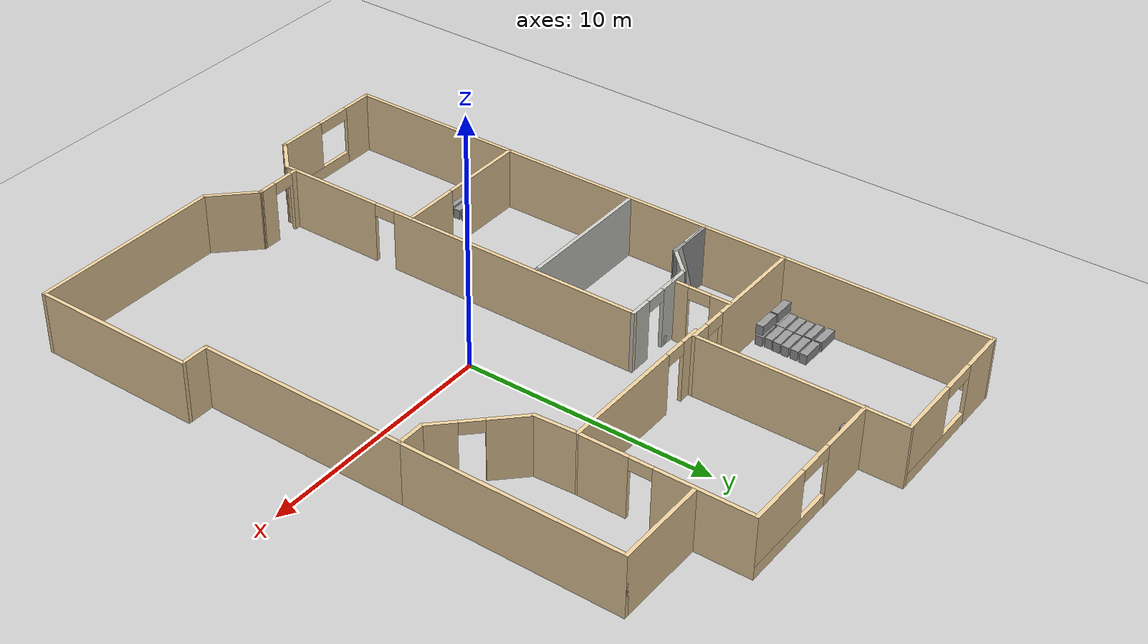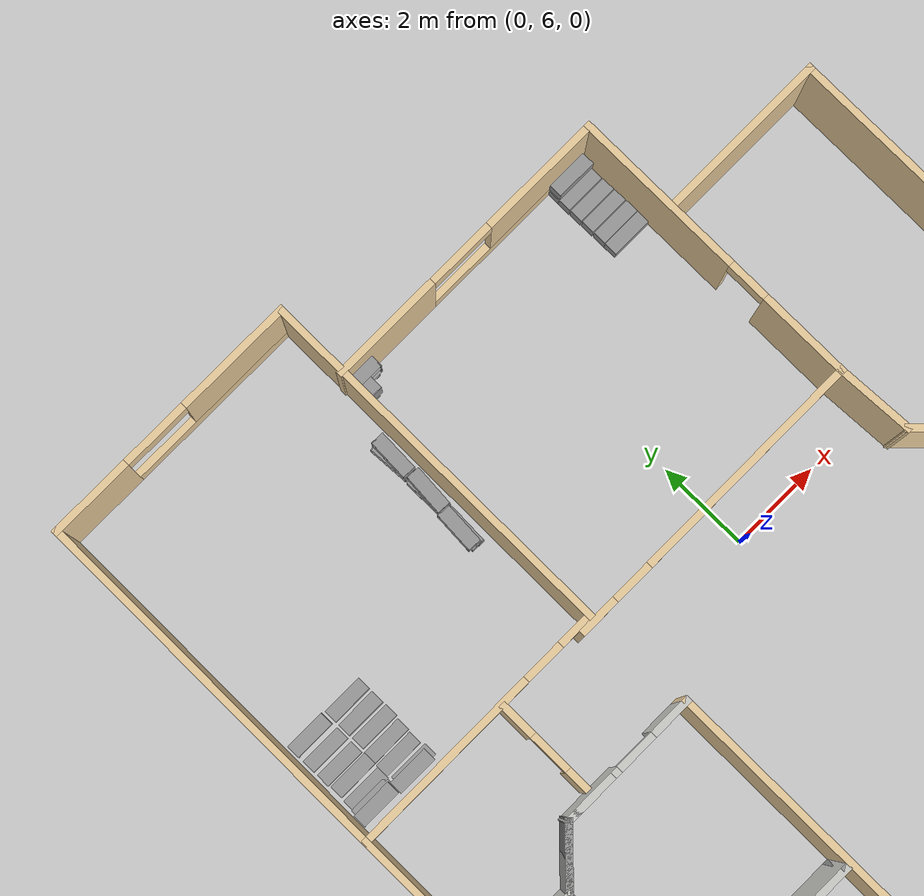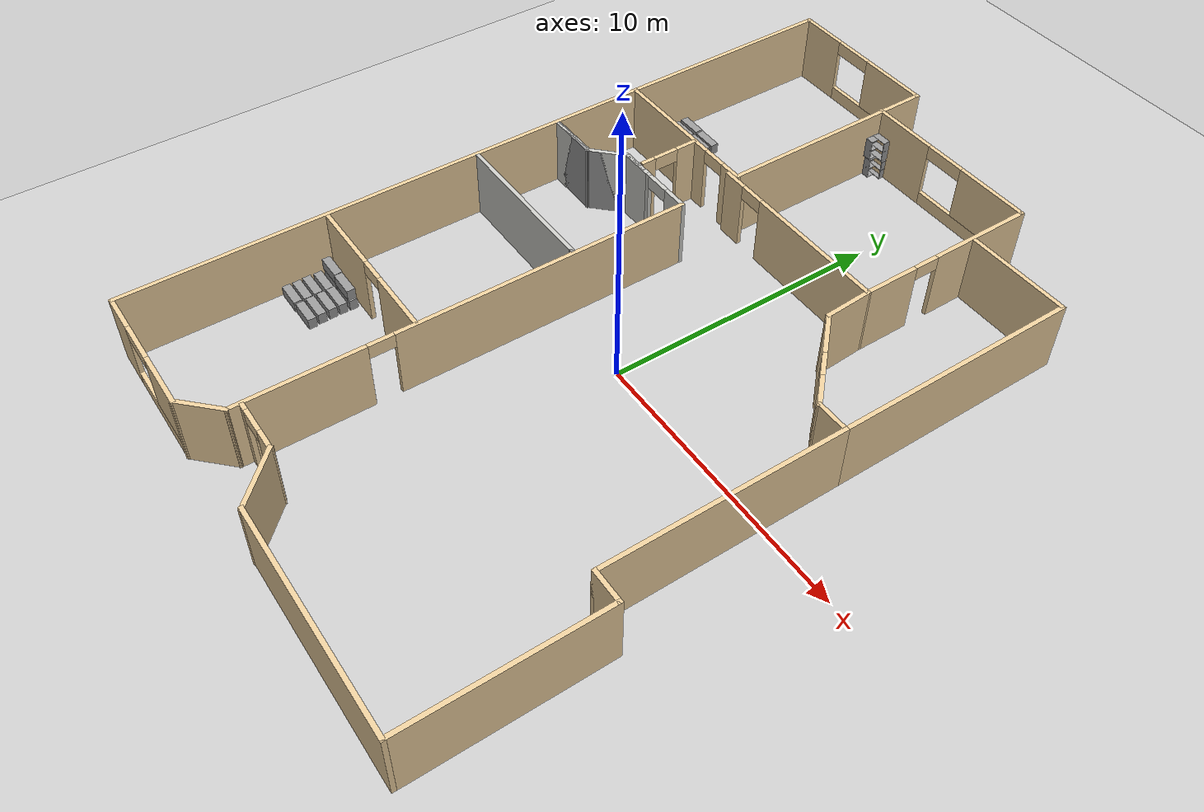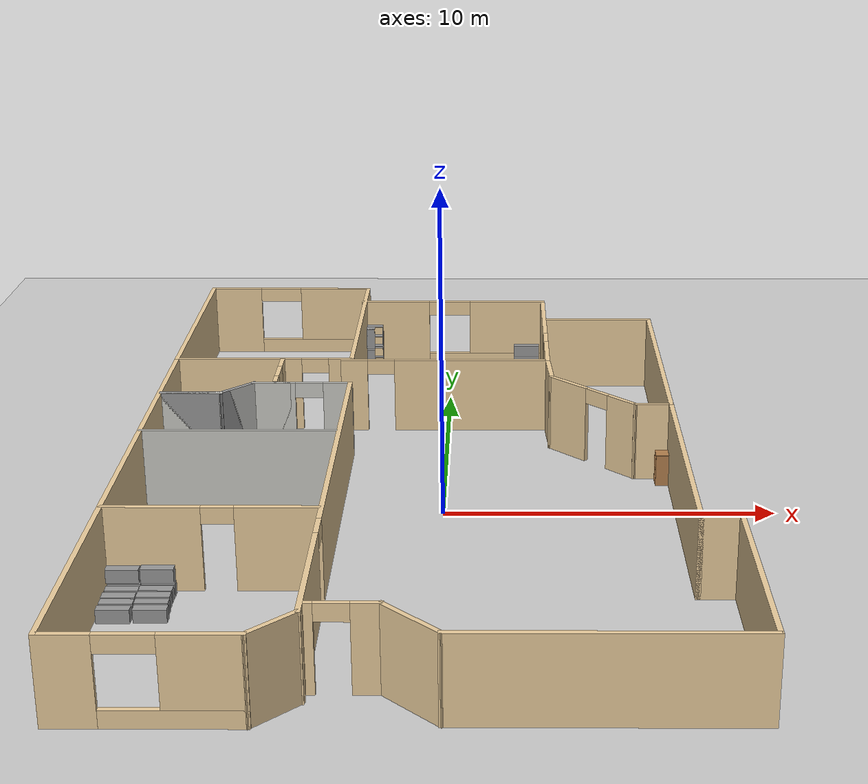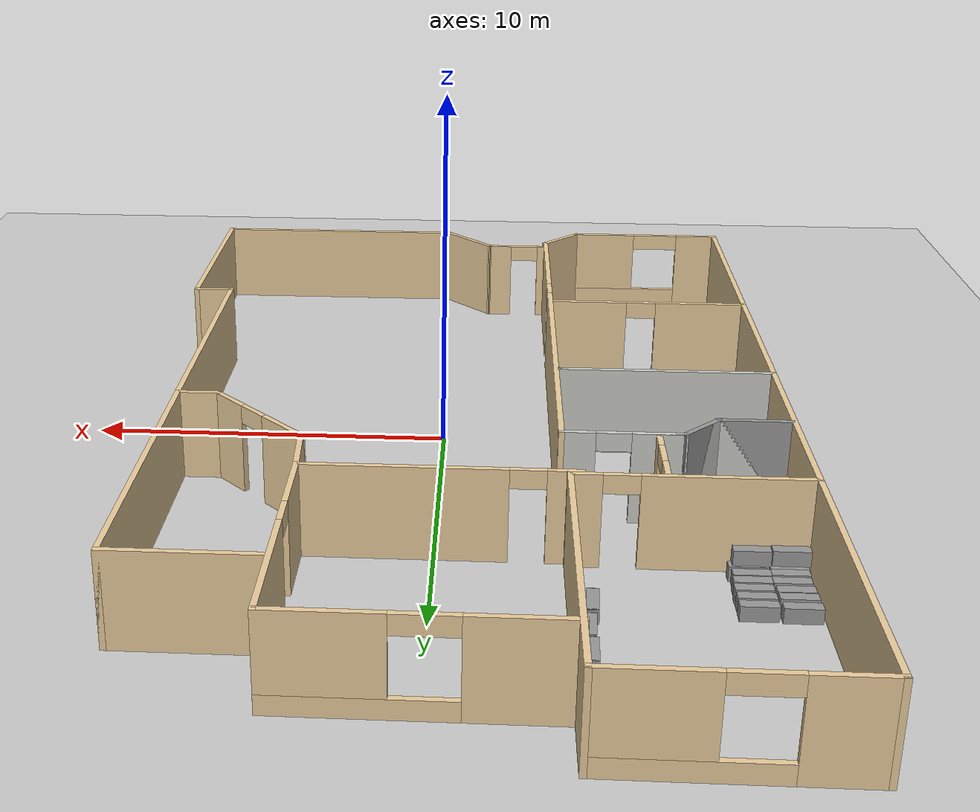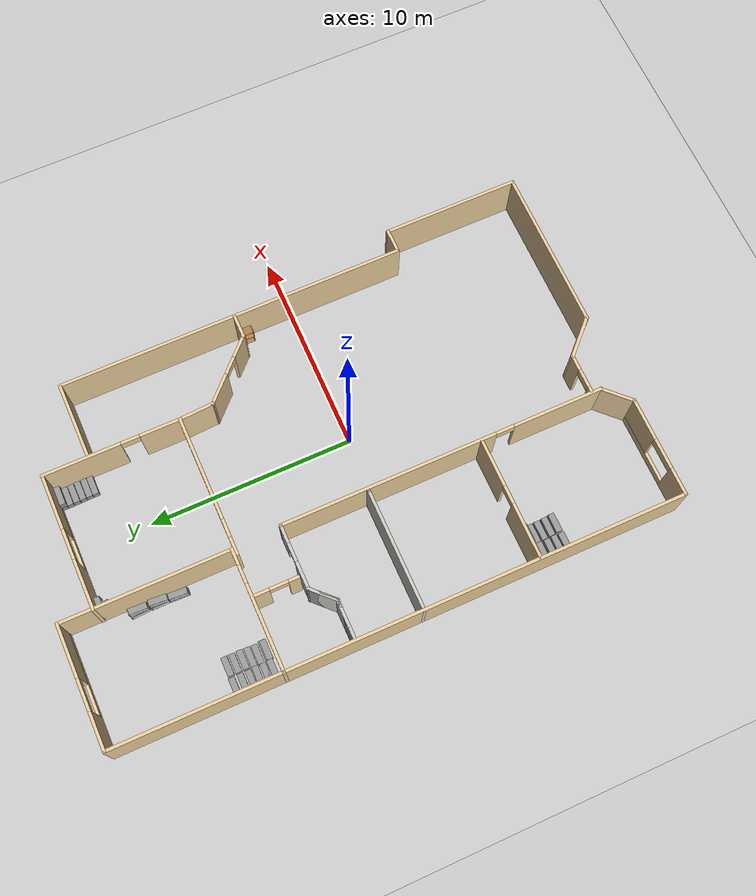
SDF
<sdf version="1.6">
 <world name="default">
  <light name="sun" type="directional">
   <pose>0 0 10 0 -0 0</pose>
   <diffuse>0.8 0.8 0.8 1</diffuse>
   <specular>0.2 0.2 0.2 1</specular>
   <attenuation>
    <range>1000</range>
    <constant>0.9</constant>
    <linear>0.01</linear>
    <quadratic>0.001</quadratic>
   </attenuation>
   <direction>-0.5 0.1 -0.9</direction>
  </light>
  <gravity>0 0 -9.8</gravity>
  <magnetic_field>6e-06 2.3e-05 -4.2e-05</magnetic_field>
  <atmosphere type="adiabatic"/>
  <physics name="default_physics" default="0" type="ode">
   <max_step_size>0.001</max_step_size>
   <real_time_factor>1</real_time_factor>
   <real_time_update_rate>1000</real_time_update_rate>
  </physics>
  <scene><ambient>0.4 0.4 0.4 1</ambient><background>0.7 0.7 0.7 1</background><shadows>1</shadows></scene>
  <spherical_coordinates>
   <surface_model>EARTH_WGS84</surface_model>
   <latitude_deg>0</latitude_deg>
   <longitude_deg>0</longitude_deg>
   <elevation>0</elevation>
   <heading_deg>0</heading_deg>
  </spherical_coordinates>
  <model name="Fleetwood.sdf">
   <pose>-0.47427 1.4205 0 0 -0 0</pose>
   <link name="Wall_28">
    <pose>-5.70288 13.7405 0 0 -0 0</pose>
    <visual name="Wall_28_Visual_0">
     <pose>-2.06151 0 1.25 0 -0 0</pose>
     <geometry><box><size>1.87698 0.15 2.5</size></box></geometry>
     <material>
      <script><uri>file://media/materials/scripts/gazebo.material</uri><name>Gazebo/Grey</name></script>
      <ambient>0.921569 0.807843 0.615686 1</ambient>
     </material>
     <meta><layer>0</layer></meta>
    </visual>
    <collision name="Wall_28_Collision_0">
     <geometry><box><size>1.87698 0.15 2.5</size></box></geometry>
     <pose>-2.06151 0 1.25 0 -0 0</pose>
    </collision>
    <visual name="Wall_28_Visual_1">
     <pose>0.938493 0 0.25 0 -0 0</pose>
     <geometry><box><size>4.12301 0.15 0.5</size></box></geometry>
     <material>
      <script><uri>file://media/materials/scripts/gazebo.material</uri><name>Gazebo/Grey</name></script>
      <ambient>0.921569 0.807843 0.615686 1</ambient>
     </material>
     <meta><layer>0</layer></meta>
    </visual>
    <collision name="Wall_28_Collision_1">
     <geometry><box><size>4.12301 0.15 0.5</size></box></geometry>
     <pose>0.938493 0 0.25 0 -0 0</pose>
    </collision>
    <visual name="Wall_28_Visual_2">
     <pose>1.68849 0 1.5 0 -0 0</pose>
     <geometry><box><size>2.62302 0.15 2</size></box></geometry>
     <material>
      <script><uri>file://media/materials/scripts/gazebo.material</uri><name>Gazebo/Grey</name></script>
      <ambient>0.921569 0.807843 0.615686 1</ambient>
     </material>
     <meta><layer>0</layer></meta>
    </visual>
    <collision name="Wall_28_Collision_2">
     <geometry><box><size>2.62302 0.15 2</size></box></geometry>
     <pose>1.68849 0 1.5 0 -0 0</pose>
    </collision>
    <visual name="Wall_28_Visual_3">
     <pose>-0.373015 0 2.25 0 -0 0</pose>
     <geometry><box><size>1.5 0.15 0.5</size></box></geometry>
     <material>
      <script><uri>file://media/materials/scripts/gazebo.material</uri><name>Gazebo/Grey</name></script>
      <ambient>0.921569 0.807843 0.615686 1</ambient>
     </material>
     <meta><layer>0</layer></meta>
    </visual>
    <collision name="Wall_28_Collision_3">
     <geometry><box><size>1.5 0.15 0.5</size></box></geometry>
     <pose>-0.373015 0 2.25 0 -0 0</pose>
    </collision>
   </link>
   <link name="Wall_29">
    <collision name="Wall_29_Collision">
     <geometry><box><size>8.25 0.15 2.5</size></box></geometry>
     <pose>0 0 1.25 0 -0 0</pose>
    </collision>
    <visual name="Wall_29_Visual">
     <pose>0 0 1.25 0 -0 0</pose>
     <geometry><box><size>8.25 0.15 2.5</size></box></geometry>
     <material>
      <script><uri>file://media/materials/scripts/gazebo.material</uri><name>Gazebo/Grey</name></script>
      <ambient>0.921569 0.807843 0.615686 1</ambient>
     </material>
     <meta><layer>0</layer></meta>
    </visual>
    <pose>-2.77788 9.69053 0 0 -0 -1.5708</pose>
   </link>
   <link name="Wall_30">
    <pose>-5.70288 5.64053 0 0 -0 3.14159</pose>
    <visual name="Wall_30_Visual_0">
     <pose>-2.5763 0 1.25 0 -0 0</pose>
     <geometry><box><size>0.8474 0.15 2.5</size></box></geometry>
     <material>
      <script><uri>file://media/materials/scripts/gazebo.material</uri><name>Gazebo/Grey</name></script>
      <ambient>0.921569 0.807843 0.615686 1</ambient>
     </material>
     <meta><layer>0</layer></meta>
    </visual>
    <collision name="Wall_30_Collision_0">
     <geometry><box><size>0.8474 0.15 2.5</size></box></geometry>
     <pose>-2.5763 0 1.25 0 -0 0</pose>
    </collision>
    <visual name="Wall_30_Visual_1">
     <pose>0.8737 0 1.25 0 -0 0</pose>
     <geometry><box><size>4.2526 0.15 2.5</size></box></geometry>
     <material>
      <script><uri>file://media/materials/scripts/gazebo.material</uri><name>Gazebo/Grey</name></script>
      <ambient>0.921569 0.807843 0.615686 1</ambient>
     </material>
     <meta><layer>0</layer></meta>
    </visual>
    <collision name="Wall_30_Collision_1">
     <geometry><box><size>4.2526 0.15 2.5</size></box></geometry>
     <pose>0.8737 0 1.25 0 -0 0</pose>
    </collision>
    <visual name="Wall_30_Visual_2">
     <pose>-1.7026 0 2.25 0 -0 0</pose>
     <geometry><box><size>0.9 0.15 0.5</size></box></geometry>
     <material>
      <script><uri>file://media/materials/scripts/gazebo.material</uri><name>Gazebo/Grey</name></script>
      <ambient>0.921569 0.807843 0.615686 1</ambient>
     </material>
     <meta><layer>0</layer></meta>
    </visual>
    <collision name="Wall_30_Collision_2">
     <geometry><box><size>0.9 0.15 0.5</size></box></geometry>
     <pose>-1.7026 0 2.25 0 -0 0</pose>
    </collision>
   </link>
   <link name="Wall_31">
    <collision name="Wall_31_Collision">
     <geometry><box><size>8.25 0.15 2.5</size></box></geometry>
     <pose>0 0 1.25 0 -0 0</pose>
    </collision>
    <visual name="Wall_31_Visual">
     <pose>0 0 1.25 0 -0 0</pose>
     <geometry><box><size>8.25 0.15 2.5</size></box></geometry>
     <material>
      <script><uri>file://media/materials/scripts/gazebo.material</uri><name>Gazebo/Grey</name></script>
      <ambient>0.921569 0.807843 0.615686 1</ambient>
     </material>
     <meta><layer>0</layer></meta>
    </visual>
    <pose>-8.62788 9.69053 0 0 -0 1.5708</pose>
   </link>
   <link name="Wall_33">
    <pose>0.490642 12.1073 0 0 -0 0</pose>
    <visual name="Wall_33_Visual_0">
     <pose>-2.13027 0 1.25 0 -0 0</pose>
     <geometry><box><size>2.48946 0.15 2.5</size></box></geometry>
     <material>
      <script><uri>file://media/materials/scripts/gazebo.material</uri><name>Gazebo/Grey</name></script>
      <ambient>0.921569 0.807843 0.615686 1</ambient>
     </material>
     <meta><layer>0</layer></meta>
    </visual>
    <collision name="Wall_33_Collision_0">
     <geometry><box><size>2.48946 0.15 2.5</size></box></geometry>
     <pose>-2.13027 0 1.25 0 -0 0</pose>
    </collision>
    <visual name="Wall_33_Visual_1">
     <pose>1.24473 0 0.25 0 -0 0</pose>
     <geometry><box><size>4.26054 0.15 0.5</size></box></geometry>
     <material>
      <script><uri>file://media/materials/scripts/gazebo.material</uri><name>Gazebo/Grey</name></script>
      <ambient>0.921569 0.807843 0.615686 1</ambient>
     </material>
     <meta><layer>0</layer></meta>
    </visual>
    <collision name="Wall_33_Collision_1">
     <geometry><box><size>4.26054 0.15 0.5</size></box></geometry>
     <pose>1.24473 0 0.25 0 -0 0</pose>
    </collision>
    <visual name="Wall_33_Visual_2">
     <pose>1.99473 0 1.5 0 -0 0</pose>
     <geometry><box><size>2.76054 0.15 2</size></box></geometry>
     <material>
      <script><uri>file://media/materials/scripts/gazebo.material</uri><name>Gazebo/Grey</name></script>
      <ambient>0.921569 0.807843 0.615686 1</ambient>
     </material>
     <meta><layer>0</layer></meta>
    </visual>
    <collision name="Wall_33_Collision_2">
     <geometry><box><size>2.76054 0.15 2</size></box></geometry>
     <pose>1.99473 0 1.5 0 -0 0</pose>
    </collision>
    <visual name="Wall_33_Visual_3">
     <pose>-0.135539 0 2.25 0 -0 0</pose>
     <geometry><box><size>1.5 0.15 0.5</size></box></geometry>
     <material>
      <script><uri>file://media/materials/scripts/gazebo.material</uri><name>Gazebo/Grey</name></script>
      <ambient>0.921569 0.807843 0.615686 1</ambient>
     </material>
     <meta><layer>0</layer></meta>
    </visual>
    <collision name="Wall_33_Collision_3">
     <geometry><box><size>1.5 0.15 0.5</size></box></geometry>
     <pose>-0.135539 0 2.25 0 -0 0</pose>
    </collision>
   </link>
   <link name="Wall_34">
    <pose>3.79064 8.80726 0 0 -0 -1.5708</pose>
    <visual name="Wall_34_Visual_0">
     <pose>-1.46987 0 1.25 0 -0 0</pose>
     <geometry><box><size>3.81026 0.15 2.5</size></box></geometry>
     <material>
      <script><uri>file://media/materials/scripts/gazebo.material</uri><name>Gazebo/Grey</name></script>
      <ambient>0.921569 0.807843 0.615686 1</ambient>
     </material>
     <meta><layer>0</layer></meta>
    </visual>
    <collision name="Wall_34_Collision_0">
     <geometry><box><size>3.81026 0.15 2.5</size></box></geometry>
     <pose>-1.46987 0 1.25 0 -0 0</pose>
    </collision>
    <visual name="Wall_34_Visual_1">
     <pose>2.35513 0 1.25 0 -0 0</pose>
     <geometry><box><size>2.03974 0.15 2.5</size></box></geometry>
     <material>
      <script><uri>file://media/materials/scripts/gazebo.material</uri><name>Gazebo/Grey</name></script>
      <ambient>0.921569 0.807843 0.615686 1</ambient>
     </material>
     <meta><layer>0</layer></meta>
    </visual>
    <collision name="Wall_34_Collision_1">
     <geometry><box><size>2.03974 0.15 2.5</size></box></geometry>
     <pose>2.35513 0 1.25 0 -0 0</pose>
    </collision>
    <visual name="Wall_34_Visual_2">
     <pose>0.885255 0 2.25 0 -0 0</pose>
     <geometry><box><size>0.9 0.15 0.5</size></box></geometry>
     <material>
      <script><uri>file://media/materials/scripts/gazebo.material</uri><name>Gazebo/Grey</name></script>
      <ambient>0.921569 0.807843 0.615686 1</ambient>
     </material>
     <meta><layer>0</layer></meta>
    </visual>
    <collision name="Wall_34_Collision_2">
     <geometry><box><size>0.9 0.15 0.5</size></box></geometry>
     <pose>0.885255 0 2.25 0 -0 0</pose>
    </collision>
   </link>
   <link name="Wall_35">
    <pose>0.365642 5.50726 0 0 -0 3.14159</pose>
    <visual name="Wall_35_Visual_0">
     <pose>-0.897897 0 1.25 0 -0 0</pose>
     <geometry><box><size>5.20421 0.15 2.5</size></box></geometry>
     <material>
      <script><uri>file://media/materials/scripts/gazebo.material</uri><name>Gazebo/Grey</name></script>
      <ambient>0.921569 0.807843 0.615686 1</ambient>
     </material>
     <meta><layer>0</layer></meta>
    </visual>
    <collision name="Wall_35_Collision_0">
     <geometry><box><size>5.20421 0.15 2.5</size></box></geometry>
     <pose>-0.897897 0 1.25 0 -0 0</pose>
    </collision>
    <visual name="Wall_35_Visual_1">
     <pose>3.0521 0 1.25 0 -0 0</pose>
     <geometry><box><size>0.895794 0.15 2.5</size></box></geometry>
     <material>
      <script><uri>file://media/materials/scripts/gazebo.material</uri><name>Gazebo/Grey</name></script>
      <ambient>0.921569 0.807843 0.615686 1</ambient>
     </material>
     <meta><layer>0</layer></meta>
    </visual>
    <collision name="Wall_35_Collision_1">
     <geometry><box><size>0.895794 0.15 2.5</size></box></geometry>
     <pose>3.0521 0 1.25 0 -0 0</pose>
    </collision>
    <visual name="Wall_35_Visual_2">
     <pose>2.15421 0 2.25 0 -0 0</pose>
     <geometry><box><size>0.9 0.15 0.5</size></box></geometry>
     <material>
      <script><uri>file://media/materials/scripts/gazebo.material</uri><name>Gazebo/Grey</name></script>
      <ambient>0.921569 0.807843 0.615686 1</ambient>
     </material>
     <meta><layer>0</layer></meta>
    </visual>
    <collision name="Wall_35_Collision_2">
     <geometry><box><size>0.9 0.15 0.5</size></box></geometry>
     <pose>2.15421 0 2.25 0 -0 0</pose>
    </collision>
   </link>
   <link name="Wall_37">
    <collision name="Wall_37_Collision">
     <geometry><box><size>3.75 0.15 2.5</size></box></geometry>
     <pose>0 0 1.25 0 -0 0</pose>
    </collision>
    <visual name="Wall_37_Visual">
     <pose>0 0 1.25 0 -0 0</pose>
     <geometry><box><size>3.75 0.15 2.5</size></box></geometry>
     <material>
      <script><uri>file://media/materials/scripts/gazebo.material</uri><name>Gazebo/Grey</name></script>
      <ambient>0.921569 0.807843 0.615686 1</ambient>
     </material>
     <meta><layer>0</layer></meta>
    </visual>
    <pose>5.72788 9.92957 0 0 -0 0</pose>
   </link>
   <link name="Wall_38">
    <collision name="Wall_38_Collision">
     <geometry><box><size>8.75 0.15 2.5</size></box></geometry>
     <pose>0 0 1.25 0 -0 0</pose>
    </collision>
    <visual name="Wall_38_Visual">
     <pose>0 0 1.25 0 -0 0</pose>
     <geometry><box><size>8.75 0.15 2.5</size></box></geometry>
     <material>
      <script><uri>file://media/materials/scripts/gazebo.material</uri><name>Gazebo/Grey</name></script>
      <ambient>0.921569 0.807843 0.615686 1</ambient>
     </material>
     <meta><layer>0</layer></meta>
    </visual>
    <pose>7.52788 5.62957 0 0 -0 -1.5708</pose>
   </link>
   <link name="Wall_39">
    <collision name="Wall_39_Collision">
     <geometry><box><size>1.25 0.15 2.5</size></box></geometry>
     <pose>0 0 1.25 0 -0 0</pose>
    </collision>
    <visual name="Wall_39_Visual">
     <pose>0 0 1.25 0 -0 0</pose>
     <geometry><box><size>1.25 0.15 2.5</size></box></geometry>
     <material>
      <script><uri>file://media/materials/scripts/gazebo.material</uri><name>Gazebo/Grey</name></script>
      <ambient>0.921569 0.807843 0.615686 1</ambient>
     </material>
     <meta><layer>0</layer></meta>
    </visual>
    <pose>6.97788 1.32957 0 0 -0 3.14159</pose>
   </link>
   <link name="Wall_40">
    <pose>5.15509 2.60236 0 0 -0 2.35619</pose>
    <visual name="Wall_40_Visual_0">
     <pose>-1.2659 0 1.25 0 -0 0</pose>
     <geometry><box><size>1.2182 0.15 2.5</size></box></geometry>
     <material>
      <script><uri>file://media/materials/scripts/gazebo.material</uri><name>Gazebo/Grey</name></script>
      <ambient>0.921569 0.807843 0.615686 1</ambient>
     </material>
     <meta><layer>0</layer></meta>
    </visual>
    <collision name="Wall_40_Collision_0">
     <geometry><box><size>1.2182 0.15 2.5</size></box></geometry>
     <pose>-1.2659 0 1.25 0 -0 0</pose>
    </collision>
    <visual name="Wall_40_Visual_1">
     <pose>1.0591 0 1.25 0 -0 0</pose>
     <geometry><box><size>1.6318 0.15 2.5</size></box></geometry>
     <material>
      <script><uri>file://media/materials/scripts/gazebo.material</uri><name>Gazebo/Grey</name></script>
      <ambient>0.921569 0.807843 0.615686 1</ambient>
     </material>
     <meta><layer>0</layer></meta>
    </visual>
    <collision name="Wall_40_Collision_1">
     <geometry><box><size>1.6318 0.15 2.5</size></box></geometry>
     <pose>1.0591 0 1.25 0 -0 0</pose>
    </collision>
    <visual name="Wall_40_Visual_2">
     <pose>-0.206804 0 2.25 0 -0 0</pose>
     <geometry><box><size>0.9 0.15 0.5</size></box></geometry>
     <material>
      <script><uri>file://media/materials/scripts/gazebo.material</uri><name>Gazebo/Grey</name></script>
      <ambient>0.921569 0.807843 0.615686 1</ambient>
     </material>
     <meta><layer>0</layer></meta>
    </visual>
    <collision name="Wall_40_Collision_2">
     <geometry><box><size>0.9 0.15 0.5</size></box></geometry>
     <pose>-0.206804 0 2.25 0 -0 0</pose>
    </collision>
   </link>
   <link name="Wall_41">
    <collision name="Wall_41_Collision">
     <geometry><box><size>1.78468 0.15 2.5</size></box></geometry>
     <pose>0 0 1.25 0 -0 0</pose>
    </collision>
    <visual name="Wall_41_Visual">
     <pose>0 0 1.25 0 -0 0</pose>
     <geometry><box><size>1.78468 0.15 2.5</size></box></geometry>
     <material>
      <script><uri>file://media/materials/scripts/gazebo.material</uri><name>Gazebo/Grey</name></script>
      <ambient>0.921569 0.807843 0.615686 1</ambient>
     </material>
     <meta><layer>0</layer></meta>
    </visual>
    <pose>3.83647 4.69121 0 0 -0 1.62689</pose>
   </link>
   <link name="Wall_43">
    <collision name="Wall_43_Collision">
     <geometry><box><size>19.5 0.15 2.5</size></box></geometry>
     <pose>0 0 1.25 0 -0 0</pose>
    </collision>
    <visual name="Wall_43_Visual">
     <pose>0 0 1.25 0 -0 0</pose>
     <geometry><box><size>19.5 0.15 2.5</size></box></geometry>
     <material>
      <script><uri>file://media/materials/scripts/gazebo.material</uri><name>Gazebo/Grey</name></script>
      <ambient>0.921569 0.807843 0.615686 1</ambient>
     </material>
     <meta><layer>0</layer></meta>
    </visual>
    <pose>-8.62788 -4.03447 0 0 -0 -1.5708</pose>
   </link>
   <link name="Wall_44">
    <pose>-6.20288 -13.7095 0 0 -0 0</pose>
    <visual name="Wall_44_Visual_0">
     <pose>-1.79969 0 1.25 0 -0 0</pose>
     <geometry><box><size>1.40061 0.15 2.5</size></box></geometry>
     <material>
      <script><uri>file://media/materials/scripts/gazebo.material</uri><name>Gazebo/Grey</name></script>
      <ambient>0.921569 0.807843 0.615686 1</ambient>
     </material>
     <meta><layer>0</layer></meta>
    </visual>
    <collision name="Wall_44_Collision_0">
     <geometry><box><size>1.40061 0.15 2.5</size></box></geometry>
     <pose>-1.79969 0 1.25 0 -0 0</pose>
    </collision>
    <visual name="Wall_44_Visual_1">
     <pose>0.700307 0 0.25 0 -0 0</pose>
     <geometry><box><size>3.59938 0.15 0.5</size></box></geometry>
     <material>
      <script><uri>file://media/materials/scripts/gazebo.material</uri><name>Gazebo/Grey</name></script>
      <ambient>0.921569 0.807843 0.615686 1</ambient>
     </material>
     <meta><layer>0</layer></meta>
    </visual>
    <collision name="Wall_44_Collision_1">
     <geometry><box><size>3.59938 0.15 0.5</size></box></geometry>
     <pose>0.700307 0 0.25 0 -0 0</pose>
    </collision>
    <visual name="Wall_44_Visual_2">
     <pose>1.45031 0 1.5 0 -0 0</pose>
     <geometry><box><size>2.09938 0.15 2</size></box></geometry>
     <material>
      <script><uri>file://media/materials/scripts/gazebo.material</uri><name>Gazebo/Grey</name></script>
      <ambient>0.921569 0.807843 0.615686 1</ambient>
     </material>
     <meta><layer>0</layer></meta>
    </visual>
    <collision name="Wall_44_Collision_2">
     <geometry><box><size>2.09938 0.15 2</size></box></geometry>
     <pose>1.45031 0 1.5 0 -0 0</pose>
    </collision>
    <visual name="Wall_44_Visual_3">
     <pose>-0.349385 0 2.25 0 -0 0</pose>
     <geometry><box><size>1.5 0.15 0.5</size></box></geometry>
     <material>
      <script><uri>file://media/materials/scripts/gazebo.material</uri><name>Gazebo/Grey</name></script>
      <ambient>0.921569 0.807843 0.615686 1</ambient>
     </material>
     <meta><layer>0</layer></meta>
    </visual>
    <collision name="Wall_44_Collision_3">
     <geometry><box><size>1.5 0.15 0.5</size></box></geometry>
     <pose>-0.349385 0 2.25 0 -0 0</pose>
    </collision>
   </link>
   <link name="Wall_45">
    <collision name="Wall_45_Collision">
     <geometry><box><size>1.75 0.15 2.5</size></box></geometry>
     <pose>0 0 1.25 0 -0 0</pose>
    </collision>
    <visual name="Wall_45_Visual">
     <pose>0 0 1.25 0 -0 0</pose>
     <geometry><box><size>1.75 0.15 2.5</size></box></geometry>
     <material>
      <script><uri>file://media/materials/scripts/gazebo.material</uri><name>Gazebo/Grey</name></script>
      <ambient>0.921569 0.807843 0.615686 1</ambient>
     </material>
     <meta><layer>0</layer></meta>
    </visual>
    <pose>-3.2122 -13.1438 0 0 -0 0.785398</pose>
   </link>
   <link name="Wall_46">
    <pose>-2.64651 -4.6531 0 0 -0 1.5708</pose>
    <visual name="Wall_46_Visual_0">
     <pose>-5.76354 0 1.25 0 -0 0</pose>
     <geometry><box><size>4.47293 0.15 2.5</size></box></geometry>
     <material>
      <script><uri>file://media/materials/scripts/gazebo.material</uri><name>Gazebo/Grey</name></script>
      <ambient>0.921569 0.807843 0.615686 1</ambient>
     </material>
     <meta><layer>0</layer></meta>
    </visual>
    <collision name="Wall_46_Collision_0">
     <geometry><box><size>4.47293 0.15 2.5</size></box></geometry>
     <pose>-5.76354 0 1.25 0 -0 0</pose>
    </collision>
    <visual name="Wall_46_Visual_1">
     <pose>2.68647 0 1.25 0 -0 0</pose>
     <geometry><box><size>10.6271 0.15 2.5</size></box></geometry>
     <material>
      <script><uri>file://media/materials/scripts/gazebo.material</uri><name>Gazebo/Grey</name></script>
      <ambient>0.921569 0.807843 0.615686 1</ambient>
     </material>
     <meta><layer>0</layer></meta>
    </visual>
    <collision name="Wall_46_Collision_1">
     <geometry><box><size>10.6271 0.15 2.5</size></box></geometry>
     <pose>2.68647 0 1.25 0 -0 0</pose>
    </collision>
    <visual name="Wall_46_Visual_2">
     <pose>-3.07707 0 2.25 0 -0 0</pose>
     <geometry><box><size>0.9 0.15 0.5</size></box></geometry>
     <material>
      <script><uri>file://media/materials/scripts/gazebo.material</uri><name>Gazebo/Grey</name></script>
      <ambient>0.921569 0.807843 0.615686 1</ambient>
     </material>
     <meta><layer>0</layer></meta>
    </visual>
    <collision name="Wall_46_Collision_2">
     <geometry><box><size>0.9 0.15 0.5</size></box></geometry>
     <pose>-3.07707 0 2.25 0 -0 0</pose>
    </collision>
   </link>
   <link name="Wall_47">
    <pose>-4.19651 3.2719 0 0 -0 3.14159</pose>
    <visual name="Wall_47_Visual_0">
     <pose>-1.15263 0 1.25 0 -0 0</pose>
     <geometry><box><size>0.944745 0.15 2.5</size></box></geometry>
     <material>
      <script><uri>file://media/materials/scripts/gazebo.material</uri><name>Gazebo/CeilingTiled</name></script>
      <ambient>1 1 1 1</ambient>
     </material>
     <meta><layer>0</layer></meta>
    </visual>
    <collision name="Wall_47_Collision_0">
     <geometry><box><size>0.944745 0.15 2.5</size></box></geometry>
     <pose>-1.15263 0 1.25 0 -0 0</pose>
    </collision>
    <visual name="Wall_47_Visual_1">
     <pose>0.922373 0 1.25 0 -0 0</pose>
     <geometry><box><size>1.40525 0.15 2.5</size></box></geometry>
     <material>
      <script><uri>file://media/materials/scripts/gazebo.material</uri><name>Gazebo/CeilingTiled</name></script>
      <ambient>1 1 1 1</ambient>
     </material>
     <meta><layer>0</layer></meta>
    </visual>
    <collision name="Wall_47_Collision_1">
     <geometry><box><size>1.40525 0.15 2.5</size></box></geometry>
     <pose>0.922373 0 1.25 0 -0 0</pose>
    </collision>
    <visual name="Wall_47_Visual_2">
     <pose>-0.230255 0 2.25 0 -0 0</pose>
     <geometry><box><size>0.9 0.15 0.5</size></box></geometry>
     <material>
      <script><uri>file://media/materials/scripts/gazebo.material</uri><name>Gazebo/CeilingTiled</name></script>
      <ambient>1 1 1 1</ambient>
     </material>
     <meta><layer>0</layer></meta>
    </visual>
    <collision name="Wall_47_Collision_2">
     <geometry><box><size>0.9 0.15 0.5</size></box></geometry>
     <pose>-0.230255 0 2.25 0 -0 0</pose>
    </collision>
   </link>
   <link name="Wall_48">
    <collision name="Wall_48_Collision">
     <geometry><box><size>1.5 0.15 2.5</size></box></geometry>
     <pose>0 0 1.25 0 -0 0</pose>
    </collision>
    <visual name="Wall_48_Visual">
     <pose>0 0 1.25 0 -0 0</pose>
     <geometry><box><size>1.5 0.15 2.5</size></box></geometry>
     <material>
      <script><uri>file://media/materials/scripts/gazebo.material</uri><name>Gazebo/Grey</name></script>
      <ambient>1 1 1 1</ambient>
     </material>
     <meta><layer>0</layer></meta>
    </visual>
    <pose>-6.22381 2.79461 0 0 -0 -2.35619</pose>
   </link>
   <link name="Wall_49">
    <collision name="Wall_49_Collision">
     <geometry><box><size>2 0.15 2.5</size></box></geometry>
     <pose>0 0 1.25 0 -0 0</pose>
    </collision>
    <visual name="Wall_49_Visual">
     <pose>0 0 1.25 0 -0 0</pose>
     <geometry><box><size>2 0.15 2.5</size></box></geometry>
     <material>
      <script><uri>file://media/materials/scripts/gazebo.material</uri><name>Gazebo/Grey</name></script>
      <ambient>1 1 1 1</ambient>
     </material>
     <meta><layer>0</layer></meta>
    </visual>
    <pose>-7.62611 2.31731 0 0 -0 3.14159</pose>
   </link>
   <link name="Wall_53">
    <pose>-5.08913 4.52418 0 0 -0 -1.5708</pose>
    <visual name="Wall_53_Visual_0">
     <pose>-0.717037 0 1.25 0 -0 0</pose>
     <geometry><box><size>0.815926 0.15 2.5</size></box></geometry>
     <material>
      <script><uri>file://media/materials/scripts/gazebo.material</uri><name>Gazebo/Grey</name></script>
      <ambient>0.921569 0.807843 0.615686 1</ambient>
     </material>
     <meta><layer>0</layer></meta>
    </visual>
    <collision name="Wall_53_Collision_0">
     <geometry><box><size>0.815926 0.15 2.5</size></box></geometry>
     <pose>-0.717037 0 1.25 0 -0 0</pose>
    </collision>
    <visual name="Wall_53_Visual_1">
     <pose>0.857963 0 1.25 0 -0 0</pose>
     <geometry><box><size>0.534074 0.15 2.5</size></box></geometry>
     <material>
      <script><uri>file://media/materials/scripts/gazebo.material</uri><name>Gazebo/Grey</name></script>
      <ambient>0.921569 0.807843 0.615686 1</ambient>
     </material>
     <meta><layer>0</layer></meta>
    </visual>
    <collision name="Wall_53_Collision_1">
     <geometry><box><size>0.534074 0.15 2.5</size></box></geometry>
     <pose>0.857963 0 1.25 0 -0 0</pose>
    </collision>
    <visual name="Wall_53_Visual_2">
     <pose>0.140926 0 2.25 0 -0 0</pose>
     <geometry><box><size>0.9 0.15 0.5</size></box></geometry>
     <material>
      <script><uri>file://media/materials/scripts/gazebo.material</uri><name>Gazebo/Grey</name></script>
      <ambient>0.921569 0.807843 0.615686 1</ambient>
     </material>
     <meta><layer>0</layer></meta>
    </visual>
    <collision name="Wall_53_Collision_2">
     <geometry><box><size>0.9 0.15 0.5</size></box></geometry>
     <pose>0.140926 0 2.25 0 -0 0</pose>
    </collision>
   </link>
   <link name="Wall_55">
    <collision name="Wall_55_Collision">
     <geometry><box><size>2 0.15 2.5</size></box></geometry>
     <pose>0 0 1.25 0 -0 0</pose>
    </collision>
    <visual name="Wall_55_Visual">
     <pose>0 0 1.25 0 -0 0</pose>
     <geometry><box><size>2 0.15 2.5</size></box></geometry>
     <material>
      <script><uri>file://media/materials/scripts/gazebo.material</uri><name>Gazebo/CeilingTiled</name></script>
      <ambient>1 1 1 1</ambient>
     </material>
     <meta><layer>0</layer></meta>
    </visual>
    <pose>-7.62611 2.31731 0 0 -0 0</pose>
   </link>
   <link name="Wall_56">
    <collision name="Wall_56_Collision">
     <geometry><box><size>1.5 0.15 2.5</size></box></geometry>
     <pose>0 0 1.25 0 -0 0</pose>
    </collision>
    <visual name="Wall_56_Visual">
     <pose>0 0 1.25 0 -0 0</pose>
     <geometry><box><size>1.5 0.15 2.5</size></box></geometry>
     <material>
      <script><uri>file://media/materials/scripts/gazebo.material</uri><name>Gazebo/CeilingTiled</name></script>
      <ambient>0.921569 0.807843 0.615686 1</ambient>
     </material>
     <meta><layer>0</layer></meta>
    </visual>
    <pose>-6.22381 2.79461 0 0 -0 0.785398</pose>
   </link>
   <link name="Wall_57">
    <collision name="Wall_57_Collision">
     <geometry><box><size>1.25 0.15 2.5</size></box></geometry>
     <pose>0 0 1.25 0 -0 0</pose>
    </collision>
    <visual name="Wall_57_Visual">
     <pose>0 0 1.25 0 -0 0</pose>
     <geometry><box><size>1.25 0.15 2.5</size></box></geometry>
     <material>
      <script><uri>file://media/materials/scripts/gazebo.material</uri><name>Gazebo/CeilingTiled</name></script>
      <ambient>0.921569 0.807843 0.615686 1</ambient>
     </material>
     <meta><layer>0</layer></meta>
    </visual>
    <pose>-5.19651 3.2719 0 0 -0 0</pose>
   </link>
   <link name="Wall_59">
    <collision name="Wall_59_Collision">
     <geometry><box><size>6 0.15 2.5</size></box></geometry>
     <pose>0 0 1.25 0 -0 0</pose>
    </collision>
    <visual name="Wall_59_Visual">
     <pose>0 0 1.25 0 -0 0</pose>
     <geometry><box><size>6 0.15 2.5</size></box></geometry>
     <material>
      <script><uri>file://media/materials/scripts/gazebo.material</uri><name>Gazebo/CeilingTiled</name></script>
      <ambient>1 1 1 1</ambient>
     </material>
     <meta><layer>0</layer></meta>
    </visual>
    <pose>-5.70288 -0.924873 0 0 -0 0</pose>
   </link>
   <link name="Wall_60">
    <collision name="Wall_60_Collision">
     <geometry><box><size>0.15 0.15 2.5</size></box></geometry>
     <pose>0 0 1.25 0 -0 0</pose>
    </collision>
    <visual name="Wall_60_Visual">
     <pose>0 0 1.25 0 -0 0</pose>
     <geometry><box><size>0.15 0.15 2.5</size></box></geometry>
     <material>
      <script><uri>file://media/materials/scripts/gazebo.material</uri><name>Gazebo/Grey</name></script>
      <ambient>1 1 1 1</ambient>
     </material>
     <meta><layer>0</layer></meta>
    </visual>
    <pose>-2.77788 -0.924873 0 0 -0 0</pose>
   </link>
   <link name="Wall_62">
    <pose>-5.66886 -6.53924 0 0 -0 0</pose>
    <visual name="Wall_62_Visual_0">
     <pose>-1.62228 0 1.25 0 -0 0</pose>
     <geometry><box><size>2.75543 0.15 2.5</size></box></geometry>
     <material>
      <script><uri>file://media/materials/scripts/gazebo.material</uri><name>Gazebo/Grey</name></script>
      <ambient>0.921569 0.807843 0.615686 1</ambient>
     </material>
     <meta><layer>0</layer></meta>
    </visual>
    <collision name="Wall_62_Collision_0">
     <geometry><box><size>2.75543 0.15 2.5</size></box></geometry>
     <pose>-1.62228 0 1.25 0 -0 0</pose>
    </collision>
    <visual name="Wall_62_Visual_1">
     <pose>1.82772 0 1.25 0 -0 0</pose>
     <geometry><box><size>2.34456 0.15 2.5</size></box></geometry>
     <material>
      <script><uri>file://media/materials/scripts/gazebo.material</uri><name>Gazebo/Grey</name></script>
      <ambient>0.921569 0.807843 0.615686 1</ambient>
     </material>
     <meta><layer>0</layer></meta>
    </visual>
    <collision name="Wall_62_Collision_1">
     <geometry><box><size>2.34456 0.15 2.5</size></box></geometry>
     <pose>1.82772 0 1.25 0 -0 0</pose>
    </collision>
    <visual name="Wall_62_Visual_2">
     <pose>0.205435 0 2.25 0 -0 0</pose>
     <geometry><box><size>0.9 0.15 0.5</size></box></geometry>
     <material>
      <script><uri>file://media/materials/scripts/gazebo.material</uri><name>Gazebo/Grey</name></script>
      <ambient>0.921569 0.807843 0.615686 1</ambient>
     </material>
     <meta><layer>0</layer></meta>
    </visual>
    <collision name="Wall_62_Collision_2">
     <geometry><box><size>0.9 0.15 0.5</size></box></geometry>
     <pose>0.205435 0 2.25 0 -0 0</pose>
    </collision>
   </link>
   <link name="Wall_64">
    <collision name="Wall_64_Collision">
     <geometry><box><size>8.5 0.15 2.5</size></box></geometry>
     <pose>0 0 1.25 0 -0 0</pose>
    </collision>
    <visual name="Wall_64_Visual">
     <pose>0 0 1.25 0 -0 0</pose>
     <geometry><box><size>8.5 0.15 2.5</size></box></geometry>
     <material>
      <script><uri>file://media/materials/scripts/gazebo.material</uri><name>Gazebo/Grey</name></script>
      <ambient>0.921569 0.807843 0.615686 1</ambient>
     </material>
     <meta><layer>0</layer></meta>
    </visual>
    <pose>7.52788 -2.84543 0 0 -0 -1.5708</pose>
   </link>
   <link name="Wall_65">
    <collision name="Wall_65_Collision">
     <geometry><box><size>1.25 0.15 2.5</size></box></geometry>
     <pose>0 0 1.25 0 -0 0</pose>
    </collision>
    <visual name="Wall_65_Visual">
     <pose>0 0 1.25 0 -0 0</pose>
     <geometry><box><size>1.25 0.15 2.5</size></box></geometry>
     <material>
      <script><uri>file://media/materials/scripts/gazebo.material</uri><name>Gazebo/Grey</name></script>
      <ambient>0.921569 0.807843 0.615686 1</ambient>
     </material>
     <meta><layer>0</layer></meta>
    </visual>
    <pose>8.07788 -7.02043 0 0 -0 0</pose>
   </link>
   <link name="Wall_66">
    <collision name="Wall_66_Collision">
     <geometry><box><size>6.75 0.15 2.5</size></box></geometry>
     <pose>0 0 1.25 0 -0 0</pose>
    </collision>
    <visual name="Wall_66_Visual">
     <pose>0 0 1.25 0 -0 0</pose>
     <geometry><box><size>6.75 0.15 2.5</size></box></geometry>
     <material>
      <script><uri>file://media/materials/scripts/gazebo.material</uri><name>Gazebo/Grey</name></script>
      <ambient>0.921569 0.807843 0.615686 1</ambient>
     </material>
     <meta><layer>0</layer></meta>
    </visual>
    <pose>8.62788 -10.3204 0 0 -0 -1.5708</pose>
   </link>
   <link name="Wall_67">
    <collision name="Wall_67_Collision">
     <geometry><box><size>8 0.15 2.5</size></box></geometry>
     <pose>0 0 1.25 0 -0 0</pose>
    </collision>
    <visual name="Wall_67_Visual">
     <pose>0 0 1.25 0 -0 0</pose>
     <geometry><box><size>8 0.15 2.5</size></box></geometry>
     <material>
      <script><uri>file://media/materials/scripts/gazebo.material</uri><name>Gazebo/Grey</name></script>
      <ambient>0.921569 0.807843 0.615686 1</ambient>
     </material>
     <meta><layer>0</layer></meta>
    </visual>
    <pose>4.70288 -13.6204 0 0 -0 3.14159</pose>
   </link>
   <link name="Wall_68">
    <collision name="Wall_68_Collision">
     <geometry><box><size>2.25 0.15 2.5</size></box></geometry>
     <pose>0 0 1.25 0 -0 0</pose>
    </collision>
    <visual name="Wall_68_Visual">
     <pose>0 0 1.25 0 -0 0</pose>
     <geometry><box><size>2.25 0.15 2.5</size></box></geometry>
     <material>
      <script><uri>file://media/materials/scripts/gazebo.material</uri><name>Gazebo/Grey</name></script>
      <ambient>0.921569 0.807843 0.615686 1</ambient>
     </material>
     <meta><layer>0</layer></meta>
    </visual>
    <pose>0.03542 -12.878 0 0 -0 2.35619</pose>
   </link>
   <link name="Wall_69">
    <pose>-1.63204 -12.1355 0 0 -0 3.14159</pose>
    <visual name="Wall_69_Visual_0">
     <pose>-0.595699 0 1.25 0 -0 0</pose>
     <geometry><box><size>0.808601 0.15 2.5</size></box></geometry>
     <material>
      <script><uri>file://media/materials/scripts/gazebo.material</uri><name>Gazebo/Grey</name></script>
      <ambient>0.921569 0.807843 0.615686 1</ambient>
     </material>
     <meta><layer>0</layer></meta>
    </visual>
    <collision name="Wall_69_Collision_0">
     <geometry><box><size>0.808601 0.15 2.5</size></box></geometry>
     <pose>-0.595699 0 1.25 0 -0 0</pose>
    </collision>
    <visual name="Wall_69_Visual_1">
     <pose>0.854301 0 1.25 0 -0 0</pose>
     <geometry><box><size>0.291399 0.15 2.5</size></box></geometry>
     <material>
      <script><uri>file://media/materials/scripts/gazebo.material</uri><name>Gazebo/Grey</name></script>
      <ambient>0.921569 0.807843 0.615686 1</ambient>
     </material>
     <meta><layer>0</layer></meta>
    </visual>
    <collision name="Wall_69_Collision_1">
     <geometry><box><size>0.291399 0.15 2.5</size></box></geometry>
     <pose>0.854301 0 1.25 0 -0 0</pose>
    </collision>
    <visual name="Wall_69_Visual_2">
     <pose>0.258601 0 2.25 0 -0 0</pose>
     <geometry><box><size>0.9 0.15 0.5</size></box></geometry>
     <material>
      <script><uri>file://media/materials/scripts/gazebo.material</uri><name>Gazebo/Grey</name></script>
      <ambient>0.921569 0.807843 0.615686 1</ambient>
     </material>
     <meta><layer>0</layer></meta>
    </visual>
    <collision name="Wall_69_Collision_2">
     <geometry><box><size>0.9 0.15 0.5</size></box></geometry>
     <pose>0.258601 0 2.25 0 -0 0</pose>
    </collision>
   </link>
   <static>1</static>
  </model>
  <model name="Box_36x15W">
   <link name="Wall">
    <pose>0 0 0.1985 0 -0 0</pose>
    <inertial>
     <mass>5</mass>
     <inertia><ixx>0.1022</ixx><iyy>0.4107</iyy><izz>0.3815</izz><ixy>0</ixy><ixz>0</ixz><iyz>0</iyz></inertia>
    </inertial>
    <collision name="Wall_Collision"><geometry><box><size>0.91 0.296 0.397</size></box></geometry></collision>
    <visual name="Wall_Visual">
     <geometry><box><size>0.91 0.296 0.397</size></box></geometry>
     <material>
      <script><uri>file://media/materials/scripts/gazebo.material</uri><name>Gazebo/Grey</name></script>
      <ambient>1 1 1 1</ambient>
     </material>
    </visual>
   </link>
   <static>1</static>
   <pose>2.73505 13.3468 0 0 -0 0</pose>
  </model>
  <model name="Box_36x15W_0">
   <link name="Wall">
    <pose>0 0 0.1985 0 -0 0</pose>
    <inertial>
     <mass>5</mass>
     <inertia><ixx>0.1022</ixx><iyy>0.4107</iyy><izz>0.3815</izz><ixy>0</ixy><ixz>0</ixz><iyz>0</iyz></inertia>
    </inertial>
    <collision name="Wall_Collision"><geometry><box><size>0.91 0.296 0.397</size></box></geometry></collision>
    <visual name="Wall_Visual">
     <geometry><box><size>0.91 0.296 0.397</size></box></geometry>
     <material>
      <script><uri>file://media/materials/scripts/gazebo.material</uri><name>Gazebo/Grey</name></script>
      <ambient>1 1 1 1</ambient>
     </material>
    </visual>
   </link>
   <static>1</static>
   <pose>2.73379 13.0426 0 0 -0 0</pose>
  </model>
  <model name="Box_36x15W_1">
   <link name="Wall">
    <pose>0 0 0.1985 0 -0 0</pose>
    <inertial>
     <mass>5</mass>
     <inertia><ixx>0.1022</ixx><iyy>0.4107</iyy><izz>0.3815</izz><ixy>0</ixy><ixz>0</ixz><iyz>0</iyz></inertia>
    </inertial>
    <collision name="Wall_Collision"><geometry><box><size>0.91 0.296 0.397</size></box></geometry></collision>
    <visual name="Wall_Visual">
     <geometry><box><size>0.91 0.296 0.397</size></box></geometry>
     <material>
      <script><uri>file://media/materials/scripts/gazebo.material</uri><name>Gazebo/Grey</name></script>
      <ambient>1 1 1 1</ambient>
     </material>
    </visual>
   </link>
   <static>1</static>
   <pose>2.74071 12.727 0 0 -0 0</pose>
  </model>
  <model name="Box_36x15W_2">
   <link name="Wall">
    <pose>0 0 0.1985 0 -0 0</pose>
    <inertial>
     <mass>5</mass>
     <inertia><ixx>0.1022</ixx><iyy>0.4107</iyy><izz>0.3815</izz><ixy>0</ixy><ixz>0</ixz><iyz>0</iyz></inertia>
    </inertial>
    <collision name="Wall_Collision"><geometry><box><size>0.91 0.296 0.397</size></box></geometry></collision>
    <visual name="Wall_Visual">
     <geometry><box><size>0.91 0.296 0.397</size></box></geometry>
     <material>
      <script><uri>file://media/materials/scripts/gazebo.material</uri><name>Gazebo/Grey</name></script>
      <ambient>1 1 1 1</ambient>
     </material>
    </visual>
   </link>
   <static>1</static>
   <pose>2.74763 12.4113 0 0 -0 0</pose>
  </model>
  <model name="Box_36x15W_3">
   <link name="Wall">
    <pose>0 0 0.1985 0 -0 0</pose>
    <inertial>
     <mass>5</mass>
     <inertia><ixx>0.1022</ixx><iyy>0.4107</iyy><izz>0.3815</izz><ixy>0</ixy><ixz>0</ixz><iyz>0</iyz></inertia>
    </inertial>
    <collision name="Wall_Collision"><geometry><box><size>0.91 0.296 0.397</size></box></geometry></collision>
    <visual name="Wall_Visual">
     <geometry><box><size>0.91 0.296 0.397</size></box></geometry>
     <material>
      <script><uri>file://media/materials/scripts/gazebo.material</uri><name>Gazebo/Grey</name></script>
      <ambient>1 1 1 1</ambient>
     </material>
    </visual>
   </link>
   <static>1</static>
   <pose>2.75455 12.0956 0 0 -0 0</pose>
  </model>
  <model name="Box_36x15W_4">
   <link name="Wall">
    <pose>0 0 0.1985 0 -0 0</pose>
    <inertial>
     <mass>5</mass>
     <inertia><ixx>0.1022</ixx><iyy>0.4107</iyy><izz>0.3815</izz><ixy>0</ixy><ixz>0</ixz><iyz>0</iyz></inertia>
    </inertial>
    <collision name="Wall_Collision"><geometry><box><size>0.91 0.296 0.397</size></box></geometry></collision>
    <visual name="Wall_Visual">
     <geometry><box><size>0.91 0.296 0.397</size></box></geometry>
     <material>
      <script><uri>file://media/materials/scripts/gazebo.material</uri><name>Gazebo/Grey</name></script>
      <ambient>1 1 1 1</ambient>
     </material>
    </visual>
   </link>
   <static>1</static>
   <pose>2.75329 11.7915 0 0 -0 0</pose>
  </model>
  <model name="Box_36x15W_5">
   <link name="Wall">
    <pose>0 0 0.1985 0 -0 0</pose>
    <inertial>
     <mass>5</mass>
     <inertia><ixx>0.1022</ixx><iyy>0.4107</iyy><izz>0.3815</izz><ixy>0</ixy><ixz>0</ixz><iyz>0</iyz></inertia>
    </inertial>
    <collision name="Wall_Collision"><geometry><box><size>0.91 0.296 0.397</size></box></geometry></collision>
    <visual name="Wall_Visual">
     <geometry><box><size>0.91 0.296 0.397</size></box></geometry>
     <material>
      <script><uri>file://media/materials/scripts/gazebo.material</uri><name>Gazebo/Grey</name></script>
      <ambient>1 1 1 1</ambient>
     </material>
    </visual>
   </link>
   <static>1</static>
   <pose>2.73178 13.3121 0.471526 0 -0 0</pose>
  </model>
  <model name="Wall_Cabinet_Coin_24x30W">
   <link name="Wall_10">
    <pose>0.286 -0.148 0.384 0 -0 0</pose>
    <inertial>
     <mass>2.1259</mass>
     <inertia><ixx>0.0158</ixx><iyy>0.1202</iyy><izz>0.1046</izz><ixy>0</ixy><ixz>0</ixz><iyz>0</iyz></inertia>
    </inertial>
    <collision name="Wall_10_Collision"><geometry><box><size>0.02 0.296 0.768</size></box></geometry></collision>
    <visual name="Wall_10_Visual">
     <geometry><box><size>0.02 0.296 0.768</size></box></geometry>
     <material>
      <script><uri>file://media/materials/scripts/gazebo.material</uri><name>Gazebo/Grey</name></script>
      <ambient>1 1 1 1</ambient>
     </material>
    </visual>
   </link>
   <joint name="10_16" type="fixed">
    <pose>0 0 -0.374 0 -0 0</pose>
    <parent>Wall_16</parent>
    <child>Wall_10</child>
    <axis>
     <xyz>1 0 0</xyz>
     <use_parent_model_frame>0</use_parent_model_frame>
     <limit><lower>-1e+16</lower><upper>1e+16</upper></limit>
    </axis>
   </joint>
   <joint name="10_14" type="fixed">
    <parent>Wall_14</parent>
    <child>Wall_10</child>
    <axis>
     <xyz>1 0 0</xyz>
     <use_parent_model_frame>0</use_parent_model_frame>
     <limit><lower>-1e+16</lower><upper>1e+16</upper></limit>
    </axis>
   </joint>
   <joint name="10_12" type="fixed">
    <pose>0 0 0.374 0 -0 0</pose>
    <parent>Wall_12</parent>
    <child>Wall_10</child>
    <axis>
     <xyz>1 0 0</xyz>
     <use_parent_model_frame>0</use_parent_model_frame>
     <limit><lower>-1e+16</lower><upper>1e+16</upper></limit>
    </axis>
   </joint>
   <joint name="10_29" type="fixed">
    <pose>0 -0.148 0 0 -0 0</pose>
    <parent>Wall_29</parent>
    <child>Wall_10</child>
    <axis>
     <xyz>1 0 0</xyz>
     <use_parent_model_frame>0</use_parent_model_frame>
     <limit><lower>-1e+16</lower><upper>1e+16</upper></limit>
    </axis>
   </joint>
   <link name="Wall_12">
    <pose>0.148 -0.148 0.758 0 -0 0</pose>
    <inertial>
     <mass>0.8802</mass>
     <inertia><ixx>0.0065</ixx><iyy>0.0139</iyy><izz>0.0074</izz><ixy>0</ixy><ixz>0</ixz><iyz>0</iyz></inertia>
    </inertial>
    <collision name="Wall_12_Collision"><geometry><box><size>0.296 0.296 0.02</size></box></geometry></collision>
    <visual name="Wall_12_Visual">
     <geometry><box><size>0.296 0.296 0.02</size></box></geometry>
     <material>
      <script><uri>file://media/materials/scripts/gazebo.material</uri><name>Gazebo/Grey</name></script>
      <ambient>1 1 1 1</ambient>
     </material>
    </visual>
   </link>
   <joint name="12_29" type="fixed">
    <pose>0 -0.148 0 0 -0 0</pose>
    <parent>Wall_29</parent>
    <child>Wall_12</child>
    <axis>
     <xyz>0 0 1</xyz>
     <use_parent_model_frame>0</use_parent_model_frame>
     <limit><lower>-1e+16</lower><upper>1e+16</upper></limit>
    </axis>
   </joint>
   <link name="Wall_14">
    <pose>0.148 -0.148 0.384 0 -0 0</pose>
    <inertial>
     <mass>0.8802</mass>
     <inertia><ixx>0.0065</ixx><iyy>0.0139</iyy><izz>0.0074</izz><ixy>0</ixy><ixz>0</ixz><iyz>0</iyz></inertia>
    </inertial>
    <collision name="Wall_14_Collision"><geometry><box><size>0.296 0.296 0.02</size></box></geometry></collision>
    <visual name="Wall_14_Visual">
     <geometry><box><size>0.296 0.296 0.02</size></box></geometry>
     <material>
      <script><uri>file://media/materials/scripts/gazebo.material</uri><name>Gazebo/Grey</name></script>
      <ambient>1 1 1 1</ambient>
     </material>
    </visual>
   </link>
   <joint name="14_29" type="fixed">
    <pose>0 -0.148 0 0 -0 0</pose>
    <parent>Wall_29</parent>
    <child>Wall_14</child>
    <axis>
     <xyz>0 1 0</xyz>
     <use_parent_model_frame>0</use_parent_model_frame>
     <limit><lower>-1e+16</lower><upper>1e+16</upper></limit>
    </axis>
   </joint>
   <link name="Wall_16">
    <pose>0.148 -0.148 0.01 0 -0 0</pose>
    <inertial>
     <mass>0.8802</mass>
     <inertia><ixx>0.0065</ixx><iyy>0.0139</iyy><izz>0.0074</izz><ixy>0</ixy><ixz>0</ixz><iyz>0</iyz></inertia>
    </inertial>
    <collision name="Wall_16_Collision"><geometry><box><size>0.296 0.296 0.02</size></box></geometry></collision>
    <visual name="Wall_16_Visual">
     <geometry><box><size>0.296 0.296 0.02</size></box></geometry>
     <material>
      <script><uri>file://media/materials/scripts/gazebo.material</uri><name>Gazebo/Grey</name></script>
      <ambient>1 1 1 1</ambient>
     </material>
    </visual>
   </link>
   <joint name="16_29" type="fixed">
    <pose>0 -0.148 0 0 -0 0</pose>
    <parent>Wall_29</parent>
    <child>Wall_16</child>
    <axis>
     <xyz>0 1 0</xyz>
     <use_parent_model_frame>0</use_parent_model_frame>
     <limit><lower>-1e+16</lower><upper>1e+16</upper></limit>
    </axis>
   </joint>
   <link name="Wall_18">
    <pose>-0.148 0 0.01 0 -0 0</pose>
    <inertial>
     <mass>1.6525</mass>
     <inertia><ixx>0.0491</ixx><iyy>0.0613</iyy><izz>0.0123</izz><ixy>0</ixy><ixz>0</ixz><iyz>0</iyz></inertia>
    </inertial>
    <collision name="Wall_18_Collision"><geometry><box><size>0.296 0.592 0.02</size></box></geometry></collision>
    <visual name="Wall_18_Visual">
     <geometry><box><size>0.296 0.592 0.02</size></box></geometry>
     <material>
      <script><uri>file://media/materials/scripts/gazebo.material</uri><name>Gazebo/Grey</name></script>
      <ambient>1 1 1 1</ambient>
     </material>
    </visual>
   </link>
   <joint name="18_16" type="fixed">
    <pose>0.148 -0.148 0 0 -0 0</pose>
    <parent>Wall_16</parent>
    <child>Wall_18</child>
    <axis>
     <xyz>1 0 0</xyz>
     <use_parent_model_frame>0</use_parent_model_frame>
     <limit><lower>-1e+16</lower><upper>1e+16</upper></limit>
    </axis>
   </joint>
   <joint name="18_29" type="fixed">
    <pose>0 -0.296 0 0 -0 0</pose>
    <parent>Wall_29</parent>
    <child>Wall_18</child>
    <axis>
     <xyz>0 1 0</xyz>
     <use_parent_model_frame>0</use_parent_model_frame>
     <limit><lower>-1e+16</lower><upper>1e+16</upper></limit>
    </axis>
   </joint>
   <joint name="18_27" type="fixed">
    <pose>-0.148 0 0 0 -0 0</pose>
    <parent>Wall_27</parent>
    <child>Wall_18</child>
    <axis>
     <xyz>1 0 0</xyz>
     <use_parent_model_frame>0</use_parent_model_frame>
     <limit><lower>-1e+16</lower><upper>1e+16</upper></limit>
    </axis>
   </joint>
   <joint name="18_30" type="fixed">
    <pose>0 0.296 0 0 -0 0</pose>
    <parent>Wall_30</parent>
    <child>Wall_18</child>
    <axis>
     <xyz>0 1 0</xyz>
     <use_parent_model_frame>0</use_parent_model_frame>
     <limit><lower>-1e+16</lower><upper>1e+16</upper></limit>
    </axis>
   </joint>
   <link name="Wall_20">
    <pose>-0.148 0 0.384 0 -0 0</pose>
    <inertial>
     <mass>1.6525</mass>
     <inertia><ixx>0.0491</ixx><iyy>0.0613</iyy><izz>0.0123</izz><ixy>0</ixy><ixz>0</ixz><iyz>0</iyz></inertia>
    </inertial>
    <collision name="Wall_20_Collision"><geometry><box><size>0.296 0.592 0.02</size></box></geometry></collision>
    <visual name="Wall_20_Visual">
     <geometry><box><size>0.296 0.592 0.02</size></box></geometry>
     <material>
      <script><uri>file://media/materials/scripts/gazebo.material</uri><name>Gazebo/Grey</name></script>
      <ambient>1 1 1 1</ambient>
     </material>
    </visual>
   </link>
   <joint name="20_14" type="fixed">
    <pose>0.148 -0.148 0 0 -0 0</pose>
    <parent>Wall_14</parent>
    <child>Wall_20</child>
    <axis>
     <xyz>1 0 0</xyz>
     <use_parent_model_frame>0</use_parent_model_frame>
     <limit><lower>-1e+16</lower><upper>1e+16</upper></limit>
    </axis>
   </joint>
   <joint name="20_29" type="fixed">
    <pose>0 -0.296 0 0 -0 0</pose>
    <parent>Wall_29</parent>
    <child>Wall_20</child>
    <axis>
     <xyz>0 1 0</xyz>
     <use_parent_model_frame>0</use_parent_model_frame>
     <limit><lower>-1e+16</lower><upper>1e+16</upper></limit>
    </axis>
   </joint>
   <joint name="20_27" type="fixed">
    <pose>-0.148 0 0 0 -0 0</pose>
    <parent>Wall_27</parent>
    <child>Wall_20</child>
    <axis>
     <xyz>1 0 0</xyz>
     <use_parent_model_frame>0</use_parent_model_frame>
     <limit><lower>-1e+16</lower><upper>1e+16</upper></limit>
    </axis>
   </joint>
   <joint name="20_30" type="fixed">
    <pose>0 0.296 0 0 -0 0</pose>
    <parent>Wall_30</parent>
    <child>Wall_20</child>
    <axis>
     <xyz>0 1 0</xyz>
     <use_parent_model_frame>0</use_parent_model_frame>
     <limit><lower>-1e+16</lower><upper>1e+16</upper></limit>
    </axis>
   </joint>
   <link name="Wall_22">
    <pose>-0.148 0 0.758 0 -0 0</pose>
    <inertial>
     <mass>1.6525</mass>
     <inertia><ixx>0.0491</ixx><iyy>0.0613</iyy><izz>0.0123</izz><ixy>0</ixy><ixz>0</ixz><iyz>0</iyz></inertia>
    </inertial>
    <collision name="Wall_22_Collision"><geometry><box><size>0.296 0.592 0.02</size></box></geometry></collision>
    <visual name="Wall_22_Visual">
     <geometry><box><size>0.296 0.592 0.02</size></box></geometry>
     <material>
      <script><uri>file://media/materials/scripts/gazebo.material</uri><name>Gazebo/Grey</name></script>
      <ambient>1 1 1 1</ambient>
     </material>
    </visual>
   </link>
   <joint name="22_12" type="fixed">
    <pose>0.148 -0.148 0 0 -0 0</pose>
    <parent>Wall_12</parent>
    <child>Wall_22</child>
    <axis>
     <xyz>1 0 0</xyz>
     <use_parent_model_frame>0</use_parent_model_frame>
     <limit><lower>-1e+16</lower><upper>1e+16</upper></limit>
    </axis>
   </joint>
   <joint name="22_29" type="fixed">
    <pose>0 -0.296 0 0 -0 0</pose>
    <parent>Wall_29</parent>
    <child>Wall_22</child>
    <axis>
     <xyz>0 1 0</xyz>
     <use_parent_model_frame>0</use_parent_model_frame>
     <limit><lower>-1e+16</lower><upper>1e+16</upper></limit>
    </axis>
   </joint>
   <joint name="22_27" type="fixed">
    <pose>-0.148 0 0 0 -0 0</pose>
    <parent>Wall_27</parent>
    <child>Wall_22</child>
    <axis>
     <xyz>1 0 0</xyz>
     <use_parent_model_frame>0</use_parent_model_frame>
     <limit><lower>-1e+16</lower><upper>1e+16</upper></limit>
    </axis>
   </joint>
   <joint name="22_30" type="fixed">
    <pose>0 0.296 0 0 -0 0</pose>
    <parent>Wall_30</parent>
    <child>Wall_22</child>
    <axis>
     <xyz>0 1 0</xyz>
     <use_parent_model_frame>0</use_parent_model_frame>
     <limit><lower>-1e+16</lower><upper>1e+16</upper></limit>
    </axis>
   </joint>
   <link name="Wall_27">
    <pose>-0.286 0 0.384 0 -0 0</pose>
    <inertial>
     <mass>4.2589</mass>
     <inertia><ixx>0.1266</ixx><iyy>0.3358</iyy><izz>0.2095</izz><ixy>0</ixy><ixz>0</ixz><iyz>0</iyz></inertia>
    </inertial>
    <collision name="Wall_27_Collision"><geometry><box><size>0.02 0.592 0.768</size></box></geometry></collision>
    <visual name="Wall_27_Visual">
     <geometry><box><size>0.02 0.592 0.768</size></box></geometry>
     <material>
      <script><uri>file://media/materials/scripts/gazebo.material</uri><name>Gazebo/Grey</name></script>
      <ambient>1 1 1 1</ambient>
     </material>
    </visual>
   </link>
   <joint name="27_30" type="fixed">
    <pose>0 0.296 0 0 -0 0</pose>
    <parent>Wall_30</parent>
    <child>Wall_27</child>
    <axis>
     <xyz>0 1 0</xyz>
     <use_parent_model_frame>0</use_parent_model_frame>
     <limit><lower>-1e+16</lower><upper>1e+16</upper></limit>
    </axis>
   </joint>
   <link name="Wall_29">
    <pose>0 -0.286 0.384 0 -0 0</pose>
    <inertial>
     <mass>4.3176</mass>
     <inertia><ixx>0.134</ixx><iyy>0.2091</iyy><izz>0.3428</izz><ixy>0</ixy><ixz>0</ixz><iyz>0</iyz></inertia>
    </inertial>
    <collision name="Wall_29_Collision"><geometry><box><size>0.592 0.02 0.768</size></box></geometry></collision>
    <visual name="Wall_29_Visual">
     <geometry><box><size>0.592 0.02 0.768</size></box></geometry>
     <material>
      <script><uri>file://media/materials/scripts/gazebo.material</uri><name>Gazebo/Grey</name></script>
      <ambient>1 1 1 1</ambient>
     </material>
    </visual>
   </link>
   <link name="Wall_30">
    <pose>-0.148 0.286 0.384 0 -0 0</pose>
    <inertial>
     <mass>2.1093</mass>
     <inertia><ixx>0.1021</ixx><iyy>0.0157</iyy><izz>0.1177</izz><ixy>0</ixy><ixz>0</ixz><iyz>0</iyz></inertia>
    </inertial>
    <collision name="Wall_30_Collision"><geometry><box><size>0.296 0.02 0.768</size></box></geometry></collision>
    <visual name="Wall_30_Visual">
     <geometry><box><size>0.296 0.02 0.768</size></box></geometry>
     <material>
      <script><uri>file://media/materials/scripts/gazebo.material</uri><name>Gazebo/Grey</name></script>
      <ambient>1 1 1 1</ambient>
     </material>
    </visual>
   </link>
   <static>1</static>
   <pose>-2.88429 13.1884 0.84864 0 0 -1.56746</pose>
  </model>
  <model name="Wall_Cabinet_Coin_24x30W_0">
   <link name="Wall_10">
    <pose>0.286 -0.148 0.384 0 -0 0</pose>
    <inertial>
     <mass>2.1259</mass>
     <inertia><ixx>0.0158</ixx><iyy>0.1202</iyy><izz>0.1046</izz><ixy>0</ixy><ixz>0</ixz><iyz>0</iyz></inertia>
    </inertial>
    <collision name="Wall_10_Collision"><geometry><box><size>0.02 0.296 0.768</size></box></geometry></collision>
    <visual name="Wall_10_Visual">
     <geometry><box><size>0.02 0.296 0.768</size></box></geometry>
     <material>
      <script><uri>file://media/materials/scripts/gazebo.material</uri><name>Gazebo/Grey</name></script>
      <ambient>1 1 1 1</ambient>
     </material>
    </visual>
   </link>
   <joint name="10_16" type="fixed">
    <pose>0 0 -0.374 0 -0 0</pose>
    <parent>Wall_16</parent>
    <child>Wall_10</child>
    <axis>
     <xyz>1 0 0</xyz>
     <use_parent_model_frame>0</use_parent_model_frame>
     <limit><lower>-1e+16</lower><upper>1e+16</upper></limit>
    </axis>
   </joint>
   <joint name="10_14" type="fixed">
    <parent>Wall_14</parent>
    <child>Wall_10</child>
    <axis>
     <xyz>1 0 0</xyz>
     <use_parent_model_frame>0</use_parent_model_frame>
     <limit><lower>-1e+16</lower><upper>1e+16</upper></limit>
    </axis>
   </joint>
   <joint name="10_12" type="fixed">
    <pose>0 0 0.374 0 -0 0</pose>
    <parent>Wall_12</parent>
    <child>Wall_10</child>
    <axis>
     <xyz>1 0 0</xyz>
     <use_parent_model_frame>0</use_parent_model_frame>
     <limit><lower>-1e+16</lower><upper>1e+16</upper></limit>
    </axis>
   </joint>
   <joint name="10_29" type="fixed">
    <pose>0 -0.148 0 0 -0 0</pose>
    <parent>Wall_29</parent>
    <child>Wall_10</child>
    <axis>
     <xyz>1 0 0</xyz>
     <use_parent_model_frame>0</use_parent_model_frame>
     <limit><lower>-1e+16</lower><upper>1e+16</upper></limit>
    </axis>
   </joint>
   <link name="Wall_12">
    <pose>0.148 -0.148 0.758 0 -0 0</pose>
    <inertial>
     <mass>0.8802</mass>
     <inertia><ixx>0.0065</ixx><iyy>0.0139</iyy><izz>0.0074</izz><ixy>0</ixy><ixz>0</ixz><iyz>0</iyz></inertia>
    </inertial>
    <collision name="Wall_12_Collision"><geometry><box><size>0.296 0.296 0.02</size></box></geometry></collision>
    <visual name="Wall_12_Visual">
     <geometry><box><size>0.296 0.296 0.02</size></box></geometry>
     <material>
      <script><uri>file://media/materials/scripts/gazebo.material</uri><name>Gazebo/Grey</name></script>
      <ambient>1 1 1 1</ambient>
     </material>
    </visual>
   </link>
   <joint name="12_29" type="fixed">
    <pose>0 -0.148 0 0 -0 0</pose>
    <parent>Wall_29</parent>
    <child>Wall_12</child>
    <axis>
     <xyz>0 0 1</xyz>
     <use_parent_model_frame>0</use_parent_model_frame>
     <limit><lower>-1e+16</lower><upper>1e+16</upper></limit>
    </axis>
   </joint>
   <link name="Wall_14">
    <pose>0.148 -0.148 0.384 0 -0 0</pose>
    <inertial>
     <mass>0.8802</mass>
     <inertia><ixx>0.0065</ixx><iyy>0.0139</iyy><izz>0.0074</izz><ixy>0</ixy><ixz>0</ixz><iyz>0</iyz></inertia>
    </inertial>
    <collision name="Wall_14_Collision"><geometry><box><size>0.296 0.296 0.02</size></box></geometry></collision>
    <visual name="Wall_14_Visual">
     <geometry><box><size>0.296 0.296 0.02</size></box></geometry>
     <material>
      <script><uri>file://media/materials/scripts/gazebo.material</uri><name>Gazebo/Grey</name></script>
      <ambient>1 1 1 1</ambient>
     </material>
    </visual>
   </link>
   <joint name="14_29" type="fixed">
    <pose>0 -0.148 0 0 -0 0</pose>
    <parent>Wall_29</parent>
    <child>Wall_14</child>
    <axis>
     <xyz>0 1 0</xyz>
     <use_parent_model_frame>0</use_parent_model_frame>
     <limit><lower>-1e+16</lower><upper>1e+16</upper></limit>
    </axis>
   </joint>
   <link name="Wall_16">
    <pose>0.148 -0.148 0.01 0 -0 0</pose>
    <inertial>
     <mass>0.8802</mass>
     <inertia><ixx>0.0065</ixx><iyy>0.0139</iyy><izz>0.0074</izz><ixy>0</ixy><ixz>0</ixz><iyz>0</iyz></inertia>
    </inertial>
    <collision name="Wall_16_Collision"><geometry><box><size>0.296 0.296 0.02</size></box></geometry></collision>
    <visual name="Wall_16_Visual">
     <geometry><box><size>0.296 0.296 0.02</size></box></geometry>
     <material>
      <script><uri>file://media/materials/scripts/gazebo.material</uri><name>Gazebo/Grey</name></script>
      <ambient>1 1 1 1</ambient>
     </material>
    </visual>
   </link>
   <joint name="16_29" type="fixed">
    <pose>0 -0.148 0 0 -0 0</pose>
    <parent>Wall_29</parent>
    <child>Wall_16</child>
    <axis>
     <xyz>0 1 0</xyz>
     <use_parent_model_frame>0</use_parent_model_frame>
     <limit><lower>-1e+16</lower><upper>1e+16</upper></limit>
    </axis>
   </joint>
   <link name="Wall_18">
    <pose>-0.148 0 0.01 0 -0 0</pose>
    <inertial>
     <mass>1.6525</mass>
     <inertia><ixx>0.0491</ixx><iyy>0.0613</iyy><izz>0.0123</izz><ixy>0</ixy><ixz>0</ixz><iyz>0</iyz></inertia>
    </inertial>
    <collision name="Wall_18_Collision"><geometry><box><size>0.296 0.592 0.02</size></box></geometry></collision>
    <visual name="Wall_18_Visual">
     <geometry><box><size>0.296 0.592 0.02</size></box></geometry>
     <material>
      <script><uri>file://media/materials/scripts/gazebo.material</uri><name>Gazebo/Grey</name></script>
      <ambient>1 1 1 1</ambient>
     </material>
    </visual>
   </link>
   <joint name="18_16" type="fixed">
    <pose>0.148 -0.148 0 0 -0 0</pose>
    <parent>Wall_16</parent>
    <child>Wall_18</child>
    <axis>
     <xyz>1 0 0</xyz>
     <use_parent_model_frame>0</use_parent_model_frame>
     <limit><lower>-1e+16</lower><upper>1e+16</upper></limit>
    </axis>
   </joint>
   <joint name="18_29" type="fixed">
    <pose>0 -0.296 0 0 -0 0</pose>
    <parent>Wall_29</parent>
    <child>Wall_18</child>
    <axis>
     <xyz>0 1 0</xyz>
     <use_parent_model_frame>0</use_parent_model_frame>
     <limit><lower>-1e+16</lower><upper>1e+16</upper></limit>
    </axis>
   </joint>
   <joint name="18_27" type="fixed">
    <pose>-0.148 0 0 0 -0 0</pose>
    <parent>Wall_27</parent>
    <child>Wall_18</child>
    <axis>
     <xyz>1 0 0</xyz>
     <use_parent_model_frame>0</use_parent_model_frame>
     <limit><lower>-1e+16</lower><upper>1e+16</upper></limit>
    </axis>
   </joint>
   <joint name="18_30" type="fixed">
    <pose>0 0.296 0 0 -0 0</pose>
    <parent>Wall_30</parent>
    <child>Wall_18</child>
    <axis>
     <xyz>0 1 0</xyz>
     <use_parent_model_frame>0</use_parent_model_frame>
     <limit><lower>-1e+16</lower><upper>1e+16</upper></limit>
    </axis>
   </joint>
   <link name="Wall_20">
    <pose>-0.148 0 0.384 0 -0 0</pose>
    <inertial>
     <mass>1.6525</mass>
     <inertia><ixx>0.0491</ixx><iyy>0.0613</iyy><izz>0.0123</izz><ixy>0</ixy><ixz>0</ixz><iyz>0</iyz></inertia>
    </inertial>
    <collision name="Wall_20_Collision"><geometry><box><size>0.296 0.592 0.02</size></box></geometry></collision>
    <visual name="Wall_20_Visual">
     <geometry><box><size>0.296 0.592 0.02</size></box></geometry>
     <material>
      <script><uri>file://media/materials/scripts/gazebo.material</uri><name>Gazebo/Grey</name></script>
      <ambient>1 1 1 1</ambient>
     </material>
    </visual>
   </link>
   <joint name="20_14" type="fixed">
    <pose>0.148 -0.148 0 0 -0 0</pose>
    <parent>Wall_14</parent>
    <child>Wall_20</child>
    <axis>
     <xyz>1 0 0</xyz>
     <use_parent_model_frame>0</use_parent_model_frame>
     <limit><lower>-1e+16</lower><upper>1e+16</upper></limit>
    </axis>
   </joint>
   <joint name="20_29" type="fixed">
    <pose>0 -0.296 0 0 -0 0</pose>
    <parent>Wall_29</parent>
    <child>Wall_20</child>
    <axis>
     <xyz>0 1 0</xyz>
     <use_parent_model_frame>0</use_parent_model_frame>
     <limit><lower>-1e+16</lower><upper>1e+16</upper></limit>
    </axis>
   </joint>
   <joint name="20_27" type="fixed">
    <pose>-0.148 0 0 0 -0 0</pose>
    <parent>Wall_27</parent>
    <child>Wall_20</child>
    <axis>
     <xyz>1 0 0</xyz>
     <use_parent_model_frame>0</use_parent_model_frame>
     <limit><lower>-1e+16</lower><upper>1e+16</upper></limit>
    </axis>
   </joint>
   <joint name="20_30" type="fixed">
    <pose>0 0.296 0 0 -0 0</pose>
    <parent>Wall_30</parent>
    <child>Wall_20</child>
    <axis>
     <xyz>0 1 0</xyz>
     <use_parent_model_frame>0</use_parent_model_frame>
     <limit><lower>-1e+16</lower><upper>1e+16</upper></limit>
    </axis>
   </joint>
   <link name="Wall_22">
    <pose>-0.148 0 0.758 0 -0 0</pose>
    <inertial>
     <mass>1.6525</mass>
     <inertia><ixx>0.0491</ixx><iyy>0.0613</iyy><izz>0.0123</izz><ixy>0</ixy><ixz>0</ixz><iyz>0</iyz></inertia>
    </inertial>
    <collision name="Wall_22_Collision"><geometry><box><size>0.296 0.592 0.02</size></box></geometry></collision>
    <visual name="Wall_22_Visual">
     <geometry><box><size>0.296 0.592 0.02</size></box></geometry>
     <material>
      <script><uri>file://media/materials/scripts/gazebo.material</uri><name>Gazebo/Grey</name></script>
      <ambient>1 1 1 1</ambient>
     </material>
    </visual>
   </link>
   <joint name="22_12" type="fixed">
    <pose>0.148 -0.148 0 0 -0 0</pose>
    <parent>Wall_12</parent>
    <child>Wall_22</child>
    <axis>
     <xyz>1 0 0</xyz>
     <use_parent_model_frame>0</use_parent_model_frame>
     <limit><lower>-1e+16</lower><upper>1e+16</upper></limit>
    </axis>
   </joint>
   <joint name="22_29" type="fixed">
    <pose>0 -0.296 0 0 -0 0</pose>
    <parent>Wall_29</parent>
    <child>Wall_22</child>
    <axis>
     <xyz>0 1 0</xyz>
     <use_parent_model_frame>0</use_parent_model_frame>
     <limit><lower>-1e+16</lower><upper>1e+16</upper></limit>
    </axis>
   </joint>
   <joint name="22_27" type="fixed">
    <pose>-0.148 0 0 0 -0 0</pose>
    <parent>Wall_27</parent>
    <child>Wall_22</child>
    <axis>
     <xyz>1 0 0</xyz>
     <use_parent_model_frame>0</use_parent_model_frame>
     <limit><lower>-1e+16</lower><upper>1e+16</upper></limit>
    </axis>
   </joint>
   <joint name="22_30" type="fixed">
    <pose>0 0.296 0 0 -0 0</pose>
    <parent>Wall_30</parent>
    <child>Wall_22</child>
    <axis>
     <xyz>0 1 0</xyz>
     <use_parent_model_frame>0</use_parent_model_frame>
     <limit><lower>-1e+16</lower><upper>1e+16</upper></limit>
    </axis>
   </joint>
   <link name="Wall_27">
    <pose>-0.286 0 0.384 0 -0 0</pose>
    <inertial>
     <mass>4.2589</mass>
     <inertia><ixx>0.1266</ixx><iyy>0.3358</iyy><izz>0.2095</izz><ixy>0</ixy><ixz>0</ixz><iyz>0</iyz></inertia>
    </inertial>
    <collision name="Wall_27_Collision"><geometry><box><size>0.02 0.592 0.768</size></box></geometry></collision>
    <visual name="Wall_27_Visual">
     <geometry><box><size>0.02 0.592 0.768</size></box></geometry>
     <material>
      <script><uri>file://media/materials/scripts/gazebo.material</uri><name>Gazebo/Grey</name></script>
      <ambient>1 1 1 1</ambient>
     </material>
    </visual>
   </link>
   <joint name="27_30" type="fixed">
    <pose>0 0.296 0 0 -0 0</pose>
    <parent>Wall_30</parent>
    <child>Wall_27</child>
    <axis>
     <xyz>0 1 0</xyz>
     <use_parent_model_frame>0</use_parent_model_frame>
     <limit><lower>-1e+16</lower><upper>1e+16</upper></limit>
    </axis>
   </joint>
   <link name="Wall_29">
    <pose>0 -0.286 0.384 0 -0 0</pose>
    <inertial>
     <mass>4.3176</mass>
     <inertia><ixx>0.134</ixx><iyy>0.2091</iyy><izz>0.3428</izz><ixy>0</ixy><ixz>0</ixz><iyz>0</iyz></inertia>
    </inertial>
    <collision name="Wall_29_Collision"><geometry><box><size>0.592 0.02 0.768</size></box></geometry></collision>
    <visual name="Wall_29_Visual">
     <geometry><box><size>0.592 0.02 0.768</size></box></geometry>
     <material>
      <script><uri>file://media/materials/scripts/gazebo.material</uri><name>Gazebo/Grey</name></script>
      <ambient>1 1 1 1</ambient>
     </material>
    </visual>
   </link>
   <link name="Wall_30">
    <pose>-0.148 0.286 0.384 0 -0 0</pose>
    <inertial>
     <mass>2.1093</mass>
     <inertia><ixx>0.1021</ixx><iyy>0.0157</iyy><izz>0.1177</izz><ixy>0</ixy><ixz>0</ixz><iyz>0</iyz></inertia>
    </inertial>
    <collision name="Wall_30_Collision"><geometry><box><size>0.296 0.02 0.768</size></box></geometry></collision>
    <visual name="Wall_30_Visual">
     <geometry><box><size>0.296 0.02 0.768</size></box></geometry>
     <material>
      <script><uri>file://media/materials/scripts/gazebo.material</uri><name>Gazebo/Grey</name></script>
      <ambient>1 1 1 1</ambient>
     </material>
    </visual>
   </link>
   <static>1</static>
   <pose>-2.89344 13.2666 0 0 0 -1.58641</pose>
  </model>
  <model name="Box_36x15W_6">
   <link name="Wall">
    <pose>0 0 0.1985 0 -0 0</pose>
    <inertial>
     <mass>5</mass>
     <inertia><ixx>0.1022</ixx><iyy>0.4107</iyy><izz>0.3815</izz><ixy>0</ixy><ixz>0</ixz><iyz>0</iyz></inertia>
    </inertial>
    <collision name="Wall_Collision"><geometry><box><size>0.91 0.296 0.397</size></box></geometry></collision>
    <visual name="Wall_Visual">
     <geometry><box><size>0.91 0.296 0.397</size></box></geometry>
     <material>
      <script><uri>file://media/materials/scripts/gazebo.material</uri><name>Gazebo/Grey</name></script>
      <ambient>1 1 1 1</ambient>
     </material>
    </visual>
   </link>
   <static>1</static>
   <pose>-8.52394 7.42992 0.439504 0 -0 0</pose>
  </model>
  <model name="Box_36x15W_7">
   <link name="Wall">
    <pose>0 0 0.1985 0 -0 0</pose>
    <inertial>
     <mass>5</mass>
     <inertia><ixx>0.1022</ixx><iyy>0.4107</iyy><izz>0.3815</izz><ixy>0</ixy><ixz>0</ixz><iyz>0</iyz></inertia>
    </inertial>
    <collision name="Wall_Collision"><geometry><box><size>0.91 0.296 0.397</size></box></geometry></collision>
    <visual name="Wall_Visual">
     <geometry><box><size>0.91 0.296 0.397</size></box></geometry>
     <material>
      <script><uri>file://media/materials/scripts/gazebo.material</uri><name>Gazebo/Grey</name></script>
      <ambient>1 1 1 1</ambient>
     </material>
    </visual>
   </link>
   <static>1</static>
   <pose>-8.4786 7.77155 0 0 -0 0</pose>
  </model>
  <model name="Box_36x15W_8">
   <link name="Wall">
    <pose>0 0 0.1985 0 -0 0</pose>
    <inertial>
     <mass>5</mass>
     <inertia><ixx>0.1022</ixx><iyy>0.4107</iyy><izz>0.3815</izz><ixy>0</ixy><ixz>0</ixz><iyz>0</iyz></inertia>
    </inertial>
    <collision name="Wall_Collision"><geometry><box><size>0.91 0.296 0.397</size></box></geometry></collision>
    <visual name="Wall_Visual">
     <geometry><box><size>0.91 0.296 0.397</size></box></geometry>
     <material>
      <script><uri>file://media/materials/scripts/gazebo.material</uri><name>Gazebo/Grey</name></script>
      <ambient>1 1 1 1</ambient>
     </material>
    </visual>
   </link>
   <static>1</static>
   <pose>-8.45754 8.14034 0 0 -0 0</pose>
  </model>
  <model name="Box_36x15W_9">
   <link name="Wall">
    <pose>0 0 0.1985 0 -0 0</pose>
    <inertial>
     <mass>5</mass>
     <inertia><ixx>0.1022</ixx><iyy>0.4107</iyy><izz>0.3815</izz><ixy>0</ixy><ixz>0</ixz><iyz>0</iyz></inertia>
    </inertial>
    <collision name="Wall_Collision"><geometry><box><size>0.91 0.296 0.397</size></box></geometry></collision>
    <visual name="Wall_Visual">
     <geometry><box><size>0.91 0.296 0.397</size></box></geometry>
     <material>
      <script><uri>file://media/materials/scripts/gazebo.material</uri><name>Gazebo/Grey</name></script>
      <ambient>1 1 1 1</ambient>
     </material>
    </visual>
   </link>
   <static>1</static>
   <pose>-8.48892 8.47658 -0.031016 0 -0 0</pose>
  </model>
  <model name="Box_36x15W_10">
   <link name="Wall">
    <pose>0 0 0.1985 0 -0 0</pose>
    <inertial>
     <mass>5</mass>
     <inertia><ixx>0.1022</ixx><iyy>0.4107</iyy><izz>0.3815</izz><ixy>0</ixy><ixz>0</ixz><iyz>0</iyz></inertia>
    </inertial>
    <collision name="Wall_Collision"><geometry><box><size>0.91 0.296 0.397</size></box></geometry></collision>
    <visual name="Wall_Visual">
     <geometry><box><size>0.91 0.296 0.397</size></box></geometry>
     <material>
      <script><uri>file://media/materials/scripts/gazebo.material</uri><name>Gazebo/Grey</name></script>
      <ambient>1 1 1 1</ambient>
     </material>
    </visual>
   </link>
   <static>1</static>
   <pose>-8.48932 8.85528 0 0 -0 0</pose>
  </model>
  <model name="Box_36x15W_11">
   <link name="Wall">
    <pose>0 0 0.1985 0 -0 0</pose>
    <inertial>
     <mass>5</mass>
     <inertia><ixx>0.1022</ixx><iyy>0.4107</iyy><izz>0.3815</izz><ixy>0</ixy><ixz>0</ixz><iyz>0</iyz></inertia>
    </inertial>
    <collision name="Wall_Collision"><geometry><box><size>0.91 0.296 0.397</size></box></geometry></collision>
    <visual name="Wall_Visual">
     <geometry><box><size>0.91 0.296 0.397</size></box></geometry>
     <material>
      <script><uri>file://media/materials/scripts/gazebo.material</uri><name>Gazebo/Grey</name></script>
      <ambient>1 1 1 1</ambient>
     </material>
    </visual>
   </link>
   <static>1</static>
   <pose>-8.50341 9.26638 0 0 -0 0</pose>
  </model>
  <model name="Box_36x15W_12">
   <link name="Wall">
    <pose>0 0 0.1985 0 -0 0</pose>
    <inertial>
     <mass>5</mass>
     <inertia><ixx>0.1022</ixx><iyy>0.4107</iyy><izz>0.3815</izz><ixy>0</ixy><ixz>0</ixz><iyz>0</iyz></inertia>
    </inertial>
    <collision name="Wall_Collision"><geometry><box><size>0.91 0.296 0.397</size></box></geometry></collision>
    <visual name="Wall_Visual">
     <geometry><box><size>0.91 0.296 0.397</size></box></geometry>
     <material>
      <script><uri>file://media/materials/scripts/gazebo.material</uri><name>Gazebo/Grey</name></script>
      <ambient>1 1 1 1</ambient>
     </material>
    </visual>
   </link>
   <static>1</static>
   <pose>-7.51098 7.44737 0 0 -0 0</pose>
  </model>
  <model name="Box_36x15W_13">
   <link name="Wall">
    <pose>0 0 0.1985 0 -0 0</pose>
    <inertial>
     <mass>5</mass>
     <inertia><ixx>0.1022</ixx><iyy>0.4107</iyy><izz>0.3815</izz><ixy>0</ixy><ixz>0</ixz><iyz>0</iyz></inertia>
    </inertial>
    <collision name="Wall_Collision"><geometry><box><size>0.91 0.296 0.397</size></box></geometry></collision>
    <visual name="Wall_Visual">
     <geometry><box><size>0.91 0.296 0.397</size></box></geometry>
     <material>
      <script><uri>file://media/materials/scripts/gazebo.material</uri><name>Gazebo/Grey</name></script>
      <ambient>1 1 1 1</ambient>
     </material>
    </visual>
   </link>
   <static>1</static>
   <pose>-7.56543 7.80833 0 0 -0 0</pose>
  </model>
  <model name="Box_36x15W_14">
   <link name="Wall">
    <pose>0 0 0.1985 0 -0 0</pose>
    <inertial>
     <mass>5</mass>
     <inertia><ixx>0.1022</ixx><iyy>0.4107</iyy><izz>0.3815</izz><ixy>0</ixy><ixz>0</ixz><iyz>0</iyz></inertia>
    </inertial>
    <collision name="Wall_Collision"><geometry><box><size>0.91 0.296 0.397</size></box></geometry></collision>
    <visual name="Wall_Visual">
     <geometry><box><size>0.91 0.296 0.397</size></box></geometry>
     <material>
      <script><uri>file://media/materials/scripts/gazebo.material</uri><name>Gazebo/Grey</name></script>
      <ambient>1 1 1 1</ambient>
     </material>
    </visual>
   </link>
   <static>1</static>
   <pose>-7.54111 8.14688 0 0 -0 0</pose>
  </model>
  <model name="Box_36x15W_15">
   <link name="Wall">
    <pose>0 0 0.1985 0 -0 0</pose>
    <inertial>
     <mass>5</mass>
     <inertia><ixx>0.1022</ixx><iyy>0.4107</iyy><izz>0.3815</izz><ixy>0</ixy><ixz>0</ixz><iyz>0</iyz></inertia>
    </inertial>
    <collision name="Wall_Collision"><geometry><box><size>0.91 0.296 0.397</size></box></geometry></collision>
    <visual name="Wall_Visual">
     <geometry><box><size>0.91 0.296 0.397</size></box></geometry>
     <material>
      <script><uri>file://media/materials/scripts/gazebo.material</uri><name>Gazebo/Grey</name></script>
      <ambient>1 1 1 1</ambient>
     </material>
    </visual>
   </link>
   <static>1</static>
   <pose>-7.51828 8.50087 0 0 -0 0</pose>
  </model>
  <model name="Box_36x15W_16">
   <link name="Wall">
    <pose>0 0 0.1985 0 -0 0</pose>
    <inertial>
     <mass>5</mass>
     <inertia><ixx>0.1022</ixx><iyy>0.4107</iyy><izz>0.3815</izz><ixy>0</ixy><ixz>0</ixz><iyz>0</iyz></inertia>
    </inertial>
    <collision name="Wall_Collision"><geometry><box><size>0.91 0.296 0.397</size></box></geometry></collision>
    <visual name="Wall_Visual">
     <geometry><box><size>0.91 0.296 0.397</size></box></geometry>
     <material>
      <script><uri>file://media/materials/scripts/gazebo.material</uri><name>Gazebo/Grey</name></script>
      <ambient>1 1 1 1</ambient>
     </material>
    </visual>
   </link>
   <static>1</static>
   <pose>-7.52733 8.86656 0 0 -0 0</pose>
  </model>
  <model name="Box_36x15W_17">
   <link name="Wall">
    <pose>0 0 0.1985 0 -0 0</pose>
    <inertial>
     <mass>5</mass>
     <inertia><ixx>0.1022</ixx><iyy>0.4107</iyy><izz>0.3815</izz><ixy>0</ixy><ixz>0</ixz><iyz>0</iyz></inertia>
    </inertial>
    <collision name="Wall_Collision"><geometry><box><size>0.91 0.296 0.397</size></box></geometry></collision>
    <visual name="Wall_Visual">
     <geometry><box><size>0.91 0.296 0.397</size></box></geometry>
     <material>
      <script><uri>file://media/materials/scripts/gazebo.material</uri><name>Gazebo/Grey</name></script>
      <ambient>1 1 1 1</ambient>
     </material>
    </visual>
   </link>
   <static>1</static>
   <pose>-7.52129 9.23411 0 0 -0 0</pose>
  </model>
  <model name="Box_36x15W_18">
   <link name="Wall">
    <pose>0 0 0.1985 0 -0 0</pose>
    <inertial>
     <mass>5</mass>
     <inertia><ixx>0.1022</ixx><iyy>0.4107</iyy><izz>0.3815</izz><ixy>0</ixy><ixz>0</ixz><iyz>0</iyz></inertia>
    </inertial>
    <collision name="Wall_Collision"><geometry><box><size>0.91 0.296 0.397</size></box></geometry></collision>
    <visual name="Wall_Visual">
     <geometry><box><size>0.91 0.296 0.397</size></box></geometry>
     <material>
      <script><uri>file://media/materials/scripts/gazebo.material</uri><name>Gazebo/Grey</name></script>
      <ambient>1 1 1 1</ambient>
     </material>
    </visual>
   </link>
   <static>1</static>
   <pose>-8.49675 7.54191 0 0 -0 0</pose>
  </model>
  <model name="Box_36x15W_19">
   <link name="Wall">
    <pose>0 0 0.1985 0 -0 0</pose>
    <inertial>
     <mass>5</mass>
     <inertia><ixx>0.1022</ixx><iyy>0.4107</iyy><izz>0.3815</izz><ixy>0</ixy><ixz>0</ixz><iyz>0</iyz></inertia>
    </inertial>
    <collision name="Wall_Collision"><geometry><box><size>0.91 0.296 0.397</size></box></geometry></collision>
    <visual name="Wall_Visual">
     <geometry><box><size>0.91 0.296 0.397</size></box></geometry>
     <material>
      <script><uri>file://media/materials/scripts/gazebo.material</uri><name>Gazebo/Grey</name></script>
      <ambient>1 1 1 1</ambient>
     </material>
    </visual>
   </link>
   <static>1</static>
   <pose>-7.60091 7.38368 0.394508 0 -0 0</pose>
  </model>
  <model name="Wall_Cabinet_36x15W">
   <link name="Wall_0">
    <pose>0 0 0.01 0 -0 0</pose>
    <inertial>
     <mass>1.9796</mass>
     <inertia><ixx>0.0145</ixx><iyy>0.1511</iyy><izz>0.1367</izz><ixy>0</ixy><ixz>0</ixz><iyz>0</iyz></inertia>
    </inertial>
    <collision name="Wall_0_Collision"><geometry><box><size>0.91 0.296 0.02</size></box></geometry></collision>
    <visual name="Wall_0_Visual">
     <geometry><box><size>0.91 0.296 0.02</size></box></geometry>
     <material>
      <script><uri>file://media/materials/scripts/gazebo.material</uri><name>Gazebo/Grey</name></script>
      <ambient>1 1 1 1</ambient>
     </material>
    </visual>
   </link>
   <joint name="0_2" type="fixed">
    <pose>-0.455 0 0 0 -0 0</pose>
    <parent>Wall_2</parent>
    <child>Wall_0</child>
    <axis>
     <xyz>0 0 1</xyz>
     <use_parent_model_frame>0</use_parent_model_frame>
     <limit><lower>-1e+16</lower><upper>1e+16</upper></limit>
    </axis>
   </joint>
   <joint name="0_4" type="fixed">
    <pose>0.455 0 0 0 -0 0</pose>
    <parent>Wall_4</parent>
    <child>Wall_0</child>
    <axis>
     <xyz>0 0 1</xyz>
     <use_parent_model_frame>0</use_parent_model_frame>
     <limit><lower>-1e+16</lower><upper>1e+16</upper></limit>
    </axis>
   </joint>
   <joint name="0_8" type="fixed">
    <pose>0 -0.148 0 0 -0 0</pose>
    <parent>Wall_8</parent>
    <child>Wall_0</child>
    <axis>
     <xyz>0 0 1</xyz>
     <use_parent_model_frame>0</use_parent_model_frame>
     <limit><lower>-1e+16</lower><upper>1e+16</upper></limit>
    </axis>
   </joint>
   <link name="Wall_2">
    <pose>-0.445 0 0.192 0 -0 0</pose>
    <inertial>
     <mass>0.8353</mass>
     <inertia><ixx>0.0061</ixx><iyy>0.0164</iyy><izz>0.0103</izz><ixy>0</ixy><ixz>0</ixz><iyz>0</iyz></inertia>
    </inertial>
    <collision name="Wall_2_Collision"><geometry><box><size>0.02 0.296 0.384</size></box></geometry></collision>
    <visual name="Wall_2_Visual">
     <geometry><box><size>0.02 0.296 0.384</size></box></geometry>
     <material>
      <script><uri>file://media/materials/scripts/gazebo.material</uri><name>Gazebo/Grey</name></script>
      <ambient>1 1 1 1</ambient>
     </material>
    </visual>
   </link>
   <link name="Wall_4">
    <pose>0.445 0 0.192 0 -0 0</pose>
    <inertial>
     <mass>0.8353</mass>
     <inertia><ixx>0.0061</ixx><iyy>0.0164</iyy><izz>0.0103</izz><ixy>0</ixy><ixz>0</ixz><iyz>0</iyz></inertia>
    </inertial>
    <collision name="Wall_4_Collision"><geometry><box><size>0.02 0.296 0.384</size></box></geometry></collision>
    <visual name="Wall_4_Visual">
     <geometry><box><size>0.02 0.296 0.384</size></box></geometry>
     <material>
      <script><uri>file://media/materials/scripts/gazebo.material</uri><name>Gazebo/Grey</name></script>
      <ambient>1 1 1 1</ambient>
     </material>
    </visual>
   </link>
   <link name="Wall_6">
    <pose>0 0 0.374 0 -0 0</pose>
    <inertial>
     <mass>1.9796</mass>
     <inertia><ixx>0.0145</ixx><iyy>0.1511</iyy><izz>0.1367</izz><ixy>0</ixy><ixz>0</ixz><iyz>0</iyz></inertia>
    </inertial>
    <collision name="Wall_6_Collision"><geometry><box><size>0.91 0.296 0.02</size></box></geometry></collision>
    <visual name="Wall_6_Visual">
     <geometry><box><size>0.91 0.296 0.02</size></box></geometry>
     <material>
      <script><uri>file://media/materials/scripts/gazebo.material</uri><name>Gazebo/Grey</name></script>
      <ambient>1 1 1 1</ambient>
     </material>
    </visual>
   </link>
   <joint name="6_2" type="fixed">
    <pose>-0.455 0 0 0 -0 0</pose>
    <parent>Wall_2</parent>
    <child>Wall_6</child>
    <axis>
     <xyz>0 0 1</xyz>
     <use_parent_model_frame>0</use_parent_model_frame>
     <limit><lower>-1e+16</lower><upper>1e+16</upper></limit>
    </axis>
   </joint>
   <joint name="6_4" type="fixed">
    <pose>0.455 0 0 0 -0 0</pose>
    <parent>Wall_4</parent>
    <child>Wall_6</child>
    <axis>
     <xyz>0 0 1</xyz>
     <use_parent_model_frame>0</use_parent_model_frame>
     <limit><lower>-1e+16</lower><upper>1e+16</upper></limit>
    </axis>
   </joint>
   <joint name="6_8" type="fixed">
    <pose>0 -0.148 0 0 -0 0</pose>
    <parent>Wall_8</parent>
    <child>Wall_6</child>
    <axis>
     <xyz>0 0 1</xyz>
     <use_parent_model_frame>0</use_parent_model_frame>
     <limit><lower>-1e+16</lower><upper>1e+16</upper></limit>
    </axis>
   </joint>
   <link name="Wall_8">
    <pose>0 -0.138 0.19 0 -0 0</pose>
    <inertial>
     <mass>2.5302</mass>
     <inertia><ixx>0.0305</ixx><iyy>0.1732</iyy><izz>0.2035</izz><ixy>0</ixy><ixz>0</ixz><iyz>0</iyz></inertia>
    </inertial>
    <collision name="Wall_8_Collision"><geometry><box><size>0.906 0.02 0.38</size></box></geometry></collision>
    <visual name="Wall_8_Visual">
     <geometry><box><size>0.906 0.02 0.38</size></box></geometry>
     <material>
      <script><uri>file://media/materials/scripts/gazebo.material</uri><name>Gazebo/Grey</name></script>
      <ambient>1 1 1 1</ambient>
     </material>
    </visual>
   </link>
   <joint name="8_2" type="fixed">
    <pose>-0.453 0 0 0 -0 0</pose>
    <parent>Wall_2</parent>
    <child>Wall_8</child>
    <axis>
     <xyz>0 1 0</xyz>
     <use_parent_model_frame>0</use_parent_model_frame>
     <limit><lower>-1e+16</lower><upper>1e+16</upper></limit>
    </axis>
   </joint>
   <joint name="8_4" type="fixed">
    <pose>0.453 0 0 0 -0 0</pose>
    <parent>Wall_4</parent>
    <child>Wall_8</child>
    <axis>
     <xyz>0 1 0</xyz>
     <use_parent_model_frame>0</use_parent_model_frame>
     <limit><lower>-1e+16</lower><upper>1e+16</upper></limit>
    </axis>
   </joint>
   <static>1</static>
   <pose>-3.60531 10.9273 -0 0 -0 1.58525</pose>
  </model>
  <model name="Wall_Cabinet_36x15W_0">
   <link name="Wall_0">
    <pose>0 0 0.01 0 -0 0</pose>
    <inertial>
     <mass>1.9796</mass>
     <inertia><ixx>0.0145</ixx><iyy>0.1511</iyy><izz>0.1367</izz><ixy>0</ixy><ixz>0</ixz><iyz>0</iyz></inertia>
    </inertial>
    <collision name="Wall_0_Collision"><geometry><box><size>0.91 0.296 0.02</size></box></geometry></collision>
    <visual name="Wall_0_Visual">
     <geometry><box><size>0.91 0.296 0.02</size></box></geometry>
     <material>
      <script><uri>file://media/materials/scripts/gazebo.material</uri><name>Gazebo/Grey</name></script>
      <ambient>1 1 1 1</ambient>
     </material>
    </visual>
   </link>
   <joint name="0_2" type="fixed">
    <pose>-0.455 0 0 0 -0 0</pose>
    <parent>Wall_2</parent>
    <child>Wall_0</child>
    <axis>
     <xyz>0 0 1</xyz>
     <use_parent_model_frame>0</use_parent_model_frame>
     <limit><lower>-1e+16</lower><upper>1e+16</upper></limit>
    </axis>
   </joint>
   <joint name="0_4" type="fixed">
    <pose>0.455 0 0 0 -0 0</pose>
    <parent>Wall_4</parent>
    <child>Wall_0</child>
    <axis>
     <xyz>0 0 1</xyz>
     <use_parent_model_frame>0</use_parent_model_frame>
     <limit><lower>-1e+16</lower><upper>1e+16</upper></limit>
    </axis>
   </joint>
   <joint name="0_8" type="fixed">
    <pose>0 -0.148 0 0 -0 0</pose>
    <parent>Wall_8</parent>
    <child>Wall_0</child>
    <axis>
     <xyz>0 0 1</xyz>
     <use_parent_model_frame>0</use_parent_model_frame>
     <limit><lower>-1e+16</lower><upper>1e+16</upper></limit>
    </axis>
   </joint>
   <link name="Wall_2">
    <pose>-0.445 0 0.192 0 -0 0</pose>
    <inertial>
     <mass>0.8353</mass>
     <inertia><ixx>0.0061</ixx><iyy>0.0164</iyy><izz>0.0103</izz><ixy>0</ixy><ixz>0</ixz><iyz>0</iyz></inertia>
    </inertial>
    <collision name="Wall_2_Collision"><geometry><box><size>0.02 0.296 0.384</size></box></geometry></collision>
    <visual name="Wall_2_Visual">
     <geometry><box><size>0.02 0.296 0.384</size></box></geometry>
     <material>
      <script><uri>file://media/materials/scripts/gazebo.material</uri><name>Gazebo/Grey</name></script>
      <ambient>1 1 1 1</ambient>
     </material>
    </visual>
   </link>
   <link name="Wall_4">
    <pose>0.445 0 0.192 0 -0 0</pose>
    <inertial>
     <mass>0.8353</mass>
     <inertia><ixx>0.0061</ixx><iyy>0.0164</iyy><izz>0.0103</izz><ixy>0</ixy><ixz>0</ixz><iyz>0</iyz></inertia>
    </inertial>
    <collision name="Wall_4_Collision"><geometry><box><size>0.02 0.296 0.384</size></box></geometry></collision>
    <visual name="Wall_4_Visual">
     <geometry><box><size>0.02 0.296 0.384</size></box></geometry>
     <material>
      <script><uri>file://media/materials/scripts/gazebo.material</uri><name>Gazebo/Grey</name></script>
      <ambient>1 1 1 1</ambient>
     </material>
    </visual>
   </link>
   <link name="Wall_6">
    <pose>0 0 0.374 0 -0 0</pose>
    <inertial>
     <mass>1.9796</mass>
     <inertia><ixx>0.0145</ixx><iyy>0.1511</iyy><izz>0.1367</izz><ixy>0</ixy><ixz>0</ixz><iyz>0</iyz></inertia>
    </inertial>
    <collision name="Wall_6_Collision"><geometry><box><size>0.91 0.296 0.02</size></box></geometry></collision>
    <visual name="Wall_6_Visual">
     <geometry><box><size>0.91 0.296 0.02</size></box></geometry>
     <material>
      <script><uri>file://media/materials/scripts/gazebo.material</uri><name>Gazebo/Grey</name></script>
      <ambient>1 1 1 1</ambient>
     </material>
    </visual>
   </link>
   <joint name="6_2" type="fixed">
    <pose>-0.455 0 0 0 -0 0</pose>
    <parent>Wall_2</parent>
    <child>Wall_6</child>
    <axis>
     <xyz>0 0 1</xyz>
     <use_parent_model_frame>0</use_parent_model_frame>
     <limit><lower>-1e+16</lower><upper>1e+16</upper></limit>
    </axis>
   </joint>
   <joint name="6_4" type="fixed">
    <pose>0.455 0 0 0 -0 0</pose>
    <parent>Wall_4</parent>
    <child>Wall_6</child>
    <axis>
     <xyz>0 0 1</xyz>
     <use_parent_model_frame>0</use_parent_model_frame>
     <limit><lower>-1e+16</lower><upper>1e+16</upper></limit>
    </axis>
   </joint>
   <joint name="6_8" type="fixed">
    <pose>0 -0.148 0 0 -0 0</pose>
    <parent>Wall_8</parent>
    <child>Wall_6</child>
    <axis>
     <xyz>0 0 1</xyz>
     <use_parent_model_frame>0</use_parent_model_frame>
     <limit><lower>-1e+16</lower><upper>1e+16</upper></limit>
    </axis>
   </joint>
   <link name="Wall_8">
    <pose>0 -0.138 0.19 0 -0 0</pose>
    <inertial>
     <mass>2.5302</mass>
     <inertia><ixx>0.0305</ixx><iyy>0.1732</iyy><izz>0.2035</izz><ixy>0</ixy><ixz>0</ixz><iyz>0</iyz></inertia>
    </inertial>
    <collision name="Wall_8_Collision"><geometry><box><size>0.906 0.02 0.38</size></box></geometry></collision>
    <visual name="Wall_8_Visual">
     <geometry><box><size>0.906 0.02 0.38</size></box></geometry>
     <material>
      <script><uri>file://media/materials/scripts/gazebo.material</uri><name>Gazebo/Grey</name></script>
      <ambient>1 1 1 1</ambient>
     </material>
    </visual>
   </link>
   <joint name="8_2" type="fixed">
    <pose>-0.453 0 0 0 -0 0</pose>
    <parent>Wall_2</parent>
    <child>Wall_8</child>
    <axis>
     <xyz>0 1 0</xyz>
     <use_parent_model_frame>0</use_parent_model_frame>
     <limit><lower>-1e+16</lower><upper>1e+16</upper></limit>
    </axis>
   </joint>
   <joint name="8_4" type="fixed">
    <pose>0.453 0 0 0 -0 0</pose>
    <parent>Wall_4</parent>
    <child>Wall_8</child>
    <axis>
     <xyz>0 1 0</xyz>
     <use_parent_model_frame>0</use_parent_model_frame>
     <limit><lower>-1e+16</lower><upper>1e+16</upper></limit>
    </axis>
   </joint>
   <static>1</static>
   <pose>-3.62637 9.99303 0 0 -0 1.53238</pose>
  </model>
  <model name="Wall_Cabinet_36x15W_1">
   <link name="Wall_0">
    <pose>0 0 0.01 0 -0 0</pose>
    <inertial>
     <mass>1.9796</mass>
     <inertia><ixx>0.0145</ixx><iyy>0.1511</iyy><izz>0.1367</izz><ixy>0</ixy><ixz>0</ixz><iyz>0</iyz></inertia>
    </inertial>
    <collision name="Wall_0_Collision"><geometry><box><size>0.91 0.296 0.02</size></box></geometry></collision>
    <visual name="Wall_0_Visual">
     <geometry><box><size>0.91 0.296 0.02</size></box></geometry>
     <material>
      <script><uri>file://media/materials/scripts/gazebo.material</uri><name>Gazebo/Grey</name></script>
      <ambient>1 1 1 1</ambient>
     </material>
    </visual>
   </link>
   <joint name="0_2" type="fixed">
    <pose>-0.455 0 0 0 -0 0</pose>
    <parent>Wall_2</parent>
    <child>Wall_0</child>
    <axis>
     <xyz>0 0 1</xyz>
     <use_parent_model_frame>0</use_parent_model_frame>
     <limit><lower>-1e+16</lower><upper>1e+16</upper></limit>
    </axis>
   </joint>
   <joint name="0_4" type="fixed">
    <pose>0.455 0 0 0 -0 0</pose>
    <parent>Wall_4</parent>
    <child>Wall_0</child>
    <axis>
     <xyz>0 0 1</xyz>
     <use_parent_model_frame>0</use_parent_model_frame>
     <limit><lower>-1e+16</lower><upper>1e+16</upper></limit>
    </axis>
   </joint>
   <joint name="0_8" type="fixed">
    <pose>0 -0.148 0 0 -0 0</pose>
    <parent>Wall_8</parent>
    <child>Wall_0</child>
    <axis>
     <xyz>0 0 1</xyz>
     <use_parent_model_frame>0</use_parent_model_frame>
     <limit><lower>-1e+16</lower><upper>1e+16</upper></limit>
    </axis>
   </joint>
   <link name="Wall_2">
    <pose>-0.445 0 0.192 0 -0 0</pose>
    <inertial>
     <mass>0.8353</mass>
     <inertia><ixx>0.0061</ixx><iyy>0.0164</iyy><izz>0.0103</izz><ixy>0</ixy><ixz>0</ixz><iyz>0</iyz></inertia>
    </inertial>
    <collision name="Wall_2_Collision"><geometry><box><size>0.02 0.296 0.384</size></box></geometry></collision>
    <visual name="Wall_2_Visual">
     <geometry><box><size>0.02 0.296 0.384</size></box></geometry>
     <material>
      <script><uri>file://media/materials/scripts/gazebo.material</uri><name>Gazebo/Grey</name></script>
      <ambient>1 1 1 1</ambient>
     </material>
    </visual>
   </link>
   <link name="Wall_4">
    <pose>0.445 0 0.192 0 -0 0</pose>
    <inertial>
     <mass>0.8353</mass>
     <inertia><ixx>0.0061</ixx><iyy>0.0164</iyy><izz>0.0103</izz><ixy>0</ixy><ixz>0</ixz><iyz>0</iyz></inertia>
    </inertial>
    <collision name="Wall_4_Collision"><geometry><box><size>0.02 0.296 0.384</size></box></geometry></collision>
    <visual name="Wall_4_Visual">
     <geometry><box><size>0.02 0.296 0.384</size></box></geometry>
     <material>
      <script><uri>file://media/materials/scripts/gazebo.material</uri><name>Gazebo/Grey</name></script>
      <ambient>1 1 1 1</ambient>
     </material>
    </visual>
   </link>
   <link name="Wall_6">
    <pose>0 0 0.374 0 -0 0</pose>
    <inertial>
     <mass>1.9796</mass>
     <inertia><ixx>0.0145</ixx><iyy>0.1511</iyy><izz>0.1367</izz><ixy>0</ixy><ixz>0</ixz><iyz>0</iyz></inertia>
    </inertial>
    <collision name="Wall_6_Collision"><geometry><box><size>0.91 0.296 0.02</size></box></geometry></collision>
    <visual name="Wall_6_Visual">
     <geometry><box><size>0.91 0.296 0.02</size></box></geometry>
     <material>
      <script><uri>file://media/materials/scripts/gazebo.material</uri><name>Gazebo/Grey</name></script>
      <ambient>1 1 1 1</ambient>
     </material>
    </visual>
   </link>
   <joint name="6_2" type="fixed">
    <pose>-0.455 0 0 0 -0 0</pose>
    <parent>Wall_2</parent>
    <child>Wall_6</child>
    <axis>
     <xyz>0 0 1</xyz>
     <use_parent_model_frame>0</use_parent_model_frame>
     <limit><lower>-1e+16</lower><upper>1e+16</upper></limit>
    </axis>
   </joint>
   <joint name="6_4" type="fixed">
    <pose>0.455 0 0 0 -0 0</pose>
    <parent>Wall_4</parent>
    <child>Wall_6</child>
    <axis>
     <xyz>0 0 1</xyz>
     <use_parent_model_frame>0</use_parent_model_frame>
     <limit><lower>-1e+16</lower><upper>1e+16</upper></limit>
    </axis>
   </joint>
   <joint name="6_8" type="fixed">
    <pose>0 -0.148 0 0 -0 0</pose>
    <parent>Wall_8</parent>
    <child>Wall_6</child>
    <axis>
     <xyz>0 0 1</xyz>
     <use_parent_model_frame>0</use_parent_model_frame>
     <limit><lower>-1e+16</lower><upper>1e+16</upper></limit>
    </axis>
   </joint>
   <link name="Wall_8">
    <pose>0 -0.138 0.19 0 -0 0</pose>
    <inertial>
     <mass>2.5302</mass>
     <inertia><ixx>0.0305</ixx><iyy>0.1732</iyy><izz>0.2035</izz><ixy>0</ixy><ixz>0</ixz><iyz>0</iyz></inertia>
    </inertial>
    <collision name="Wall_8_Collision"><geometry><box><size>0.906 0.02 0.38</size></box></geometry></collision>
    <visual name="Wall_8_Visual">
     <geometry><box><size>0.906 0.02 0.38</size></box></geometry>
     <material>
      <script><uri>file://media/materials/scripts/gazebo.material</uri><name>Gazebo/Grey</name></script>
      <ambient>1 1 1 1</ambient>
     </material>
    </visual>
   </link>
   <joint name="8_2" type="fixed">
    <pose>-0.453 0 0 0 -0 0</pose>
    <parent>Wall_2</parent>
    <child>Wall_8</child>
    <axis>
     <xyz>0 1 0</xyz>
     <use_parent_model_frame>0</use_parent_model_frame>
     <limit><lower>-1e+16</lower><upper>1e+16</upper></limit>
    </axis>
   </joint>
   <joint name="8_4" type="fixed">
    <pose>0.453 0 0 0 -0 0</pose>
    <parent>Wall_4</parent>
    <child>Wall_8</child>
    <axis>
     <xyz>0 1 0</xyz>
     <use_parent_model_frame>0</use_parent_model_frame>
     <limit><lower>-1e+16</lower><upper>1e+16</upper></limit>
    </axis>
   </joint>
   <static>1</static>
   <pose>-3.62012 11.8883 -0 0 -0 1.63311</pose>
  </model>
  <model name="Wall_Cabinet_36x15W_2">
   <link name="Wall_0">
    <pose>0 0 0.01 0 -0 0</pose>
    <inertial>
     <mass>1.9796</mass>
     <inertia><ixx>0.0145</ixx><iyy>0.1511</iyy><izz>0.1367</izz><ixy>0</ixy><ixz>0</ixz><iyz>0</iyz></inertia>
    </inertial>
    <collision name="Wall_0_Collision"><geometry><box><size>0.91 0.296 0.02</size></box></geometry></collision>
    <visual name="Wall_0_Visual">
     <geometry><box><size>0.91 0.296 0.02</size></box></geometry>
     <material>
      <script><uri>file://media/materials/scripts/gazebo.material</uri><name>Gazebo/Grey</name></script>
      <ambient>1 1 1 1</ambient>
     </material>
    </visual>
   </link>
   <joint name="0_2" type="fixed">
    <pose>-0.455 0 0 0 -0 0</pose>
    <parent>Wall_2</parent>
    <child>Wall_0</child>
    <axis>
     <xyz>0 0 1</xyz>
     <use_parent_model_frame>0</use_parent_model_frame>
     <limit><lower>-1e+16</lower><upper>1e+16</upper></limit>
    </axis>
   </joint>
   <joint name="0_4" type="fixed">
    <pose>0.455 0 0 0 -0 0</pose>
    <parent>Wall_4</parent>
    <child>Wall_0</child>
    <axis>
     <xyz>0 0 1</xyz>
     <use_parent_model_frame>0</use_parent_model_frame>
     <limit><lower>-1e+16</lower><upper>1e+16</upper></limit>
    </axis>
   </joint>
   <joint name="0_8" type="fixed">
    <pose>0 -0.148 0 0 -0 0</pose>
    <parent>Wall_8</parent>
    <child>Wall_0</child>
    <axis>
     <xyz>0 0 1</xyz>
     <use_parent_model_frame>0</use_parent_model_frame>
     <limit><lower>-1e+16</lower><upper>1e+16</upper></limit>
    </axis>
   </joint>
   <link name="Wall_2">
    <pose>-0.445 0 0.192 0 -0 0</pose>
    <inertial>
     <mass>0.8353</mass>
     <inertia><ixx>0.0061</ixx><iyy>0.0164</iyy><izz>0.0103</izz><ixy>0</ixy><ixz>0</ixz><iyz>0</iyz></inertia>
    </inertial>
    <collision name="Wall_2_Collision"><geometry><box><size>0.02 0.296 0.384</size></box></geometry></collision>
    <visual name="Wall_2_Visual">
     <geometry><box><size>0.02 0.296 0.384</size></box></geometry>
     <material>
      <script><uri>file://media/materials/scripts/gazebo.material</uri><name>Gazebo/Grey</name></script>
      <ambient>1 1 1 1</ambient>
     </material>
    </visual>
   </link>
   <link name="Wall_4">
    <pose>0.445 0 0.192 0 -0 0</pose>
    <inertial>
     <mass>0.8353</mass>
     <inertia><ixx>0.0061</ixx><iyy>0.0164</iyy><izz>0.0103</izz><ixy>0</ixy><ixz>0</ixz><iyz>0</iyz></inertia>
    </inertial>
    <collision name="Wall_4_Collision"><geometry><box><size>0.02 0.296 0.384</size></box></geometry></collision>
    <visual name="Wall_4_Visual">
     <geometry><box><size>0.02 0.296 0.384</size></box></geometry>
     <material>
      <script><uri>file://media/materials/scripts/gazebo.material</uri><name>Gazebo/Grey</name></script>
      <ambient>1 1 1 1</ambient>
     </material>
    </visual>
   </link>
   <link name="Wall_6">
    <pose>0 0 0.374 0 -0 0</pose>
    <inertial>
     <mass>1.9796</mass>
     <inertia><ixx>0.0145</ixx><iyy>0.1511</iyy><izz>0.1367</izz><ixy>0</ixy><ixz>0</ixz><iyz>0</iyz></inertia>
    </inertial>
    <collision name="Wall_6_Collision"><geometry><box><size>0.91 0.296 0.02</size></box></geometry></collision>
    <visual name="Wall_6_Visual">
     <geometry><box><size>0.91 0.296 0.02</size></box></geometry>
     <material>
      <script><uri>file://media/materials/scripts/gazebo.material</uri><name>Gazebo/Grey</name></script>
      <ambient>1 1 1 1</ambient>
     </material>
    </visual>
   </link>
   <joint name="6_2" type="fixed">
    <pose>-0.455 0 0 0 -0 0</pose>
    <parent>Wall_2</parent>
    <child>Wall_6</child>
    <axis>
     <xyz>0 0 1</xyz>
     <use_parent_model_frame>0</use_parent_model_frame>
     <limit><lower>-1e+16</lower><upper>1e+16</upper></limit>
    </axis>
   </joint>
   <joint name="6_4" type="fixed">
    <pose>0.455 0 0 0 -0 0</pose>
    <parent>Wall_4</parent>
    <child>Wall_6</child>
    <axis>
     <xyz>0 0 1</xyz>
     <use_parent_model_frame>0</use_parent_model_frame>
     <limit><lower>-1e+16</lower><upper>1e+16</upper></limit>
    </axis>
   </joint>
   <joint name="6_8" type="fixed">
    <pose>0 -0.148 0 0 -0 0</pose>
    <parent>Wall_8</parent>
    <child>Wall_6</child>
    <axis>
     <xyz>0 0 1</xyz>
     <use_parent_model_frame>0</use_parent_model_frame>
     <limit><lower>-1e+16</lower><upper>1e+16</upper></limit>
    </axis>
   </joint>
   <link name="Wall_8">
    <pose>0 -0.138 0.19 0 -0 0</pose>
    <inertial>
     <mass>2.5302</mass>
     <inertia><ixx>0.0305</ixx><iyy>0.1732</iyy><izz>0.2035</izz><ixy>0</ixy><ixz>0</ixz><iyz>0</iyz></inertia>
    </inertial>
    <collision name="Wall_8_Collision"><geometry><box><size>0.906 0.02 0.38</size></box></geometry></collision>
    <visual name="Wall_8_Visual">
     <geometry><box><size>0.906 0.02 0.38</size></box></geometry>
     <material>
      <script><uri>file://media/materials/scripts/gazebo.material</uri><name>Gazebo/Grey</name></script>
      <ambient>1 1 1 1</ambient>
     </material>
    </visual>
   </link>
   <joint name="8_2" type="fixed">
    <pose>-0.453 0 0 0 -0 0</pose>
    <parent>Wall_2</parent>
    <child>Wall_8</child>
    <axis>
     <xyz>0 1 0</xyz>
     <use_parent_model_frame>0</use_parent_model_frame>
     <limit><lower>-1e+16</lower><upper>1e+16</upper></limit>
    </axis>
   </joint>
   <joint name="8_4" type="fixed">
    <pose>0.453 0 0 0 -0 0</pose>
    <parent>Wall_4</parent>
    <child>Wall_8</child>
    <axis>
     <xyz>0 1 0</xyz>
     <use_parent_model_frame>0</use_parent_model_frame>
     <limit><lower>-1e+16</lower><upper>1e+16</upper></limit>
    </axis>
   </joint>
   <static>1</static>
   <pose>-3.59001 11.9077 0.410147 0 -0 1.53282</pose>
  </model>
  <model name="Wall_Cabinet_36x15W_3">
   <link name="Wall_0">
    <pose>0 0 0.01 0 -0 0</pose>
    <inertial>
     <mass>1.9796</mass>
     <inertia><ixx>0.0145</ixx><iyy>0.1511</iyy><izz>0.1367</izz><ixy>0</ixy><ixz>0</ixz><iyz>0</iyz></inertia>
    </inertial>
    <collision name="Wall_0_Collision"><geometry><box><size>0.91 0.296 0.02</size></box></geometry></collision>
    <visual name="Wall_0_Visual">
     <geometry><box><size>0.91 0.296 0.02</size></box></geometry>
     <material>
      <script><uri>file://media/materials/scripts/gazebo.material</uri><name>Gazebo/Grey</name></script>
      <ambient>1 1 1 1</ambient>
     </material>
    </visual>
   </link>
   <joint name="0_2" type="fixed">
    <pose>-0.455 0 0 0 -0 0</pose>
    <parent>Wall_2</parent>
    <child>Wall_0</child>
    <axis>
     <xyz>0 0 1</xyz>
     <use_parent_model_frame>0</use_parent_model_frame>
     <limit><lower>-1e+16</lower><upper>1e+16</upper></limit>
    </axis>
   </joint>
   <joint name="0_4" type="fixed">
    <pose>0.455 0 0 0 -0 0</pose>
    <parent>Wall_4</parent>
    <child>Wall_0</child>
    <axis>
     <xyz>0 0 1</xyz>
     <use_parent_model_frame>0</use_parent_model_frame>
     <limit><lower>-1e+16</lower><upper>1e+16</upper></limit>
    </axis>
   </joint>
   <joint name="0_8" type="fixed">
    <pose>0 -0.148 0 0 -0 0</pose>
    <parent>Wall_8</parent>
    <child>Wall_0</child>
    <axis>
     <xyz>0 0 1</xyz>
     <use_parent_model_frame>0</use_parent_model_frame>
     <limit><lower>-1e+16</lower><upper>1e+16</upper></limit>
    </axis>
   </joint>
   <link name="Wall_2">
    <pose>-0.445 0 0.192 0 -0 0</pose>
    <inertial>
     <mass>0.8353</mass>
     <inertia><ixx>0.0061</ixx><iyy>0.0164</iyy><izz>0.0103</izz><ixy>0</ixy><ixz>0</ixz><iyz>0</iyz></inertia>
    </inertial>
    <collision name="Wall_2_Collision"><geometry><box><size>0.02 0.296 0.384</size></box></geometry></collision>
    <visual name="Wall_2_Visual">
     <geometry><box><size>0.02 0.296 0.384</size></box></geometry>
     <material>
      <script><uri>file://media/materials/scripts/gazebo.material</uri><name>Gazebo/Grey</name></script>
      <ambient>1 1 1 1</ambient>
     </material>
    </visual>
   </link>
   <link name="Wall_4">
    <pose>0.445 0 0.192 0 -0 0</pose>
    <inertial>
     <mass>0.8353</mass>
     <inertia><ixx>0.0061</ixx><iyy>0.0164</iyy><izz>0.0103</izz><ixy>0</ixy><ixz>0</ixz><iyz>0</iyz></inertia>
    </inertial>
    <collision name="Wall_4_Collision"><geometry><box><size>0.02 0.296 0.384</size></box></geometry></collision>
    <visual name="Wall_4_Visual">
     <geometry><box><size>0.02 0.296 0.384</size></box></geometry>
     <material>
      <script><uri>file://media/materials/scripts/gazebo.material</uri><name>Gazebo/Grey</name></script>
      <ambient>1 1 1 1</ambient>
     </material>
    </visual>
   </link>
   <link name="Wall_6">
    <pose>0 0 0.374 0 -0 0</pose>
    <inertial>
     <mass>1.9796</mass>
     <inertia><ixx>0.0145</ixx><iyy>0.1511</iyy><izz>0.1367</izz><ixy>0</ixy><ixz>0</ixz><iyz>0</iyz></inertia>
    </inertial>
    <collision name="Wall_6_Collision"><geometry><box><size>0.91 0.296 0.02</size></box></geometry></collision>
    <visual name="Wall_6_Visual">
     <geometry><box><size>0.91 0.296 0.02</size></box></geometry>
     <material>
      <script><uri>file://media/materials/scripts/gazebo.material</uri><name>Gazebo/Grey</name></script>
      <ambient>1 1 1 1</ambient>
     </material>
    </visual>
   </link>
   <joint name="6_2" type="fixed">
    <pose>-0.455 0 0 0 -0 0</pose>
    <parent>Wall_2</parent>
    <child>Wall_6</child>
    <axis>
     <xyz>0 0 1</xyz>
     <use_parent_model_frame>0</use_parent_model_frame>
     <limit><lower>-1e+16</lower><upper>1e+16</upper></limit>
    </axis>
   </joint>
   <joint name="6_4" type="fixed">
    <pose>0.455 0 0 0 -0 0</pose>
    <parent>Wall_4</parent>
    <child>Wall_6</child>
    <axis>
     <xyz>0 0 1</xyz>
     <use_parent_model_frame>0</use_parent_model_frame>
     <limit><lower>-1e+16</lower><upper>1e+16</upper></limit>
    </axis>
   </joint>
   <joint name="6_8" type="fixed">
    <pose>0 -0.148 0 0 -0 0</pose>
    <parent>Wall_8</parent>
    <child>Wall_6</child>
    <axis>
     <xyz>0 0 1</xyz>
     <use_parent_model_frame>0</use_parent_model_frame>
     <limit><lower>-1e+16</lower><upper>1e+16</upper></limit>
    </axis>
   </joint>
   <link name="Wall_8">
    <pose>0 -0.138 0.19 0 -0 0</pose>
    <inertial>
     <mass>2.5302</mass>
     <inertia><ixx>0.0305</ixx><iyy>0.1732</iyy><izz>0.2035</izz><ixy>0</ixy><ixz>0</ixz><iyz>0</iyz></inertia>
    </inertial>
    <collision name="Wall_8_Collision"><geometry><box><size>0.906 0.02 0.38</size></box></geometry></collision>
    <visual name="Wall_8_Visual">
     <geometry><box><size>0.906 0.02 0.38</size></box></geometry>
     <material>
      <script><uri>file://media/materials/scripts/gazebo.material</uri><name>Gazebo/Grey</name></script>
      <ambient>1 1 1 1</ambient>
     </material>
    </visual>
   </link>
   <joint name="8_2" type="fixed">
    <pose>-0.453 0 0 0 -0 0</pose>
    <parent>Wall_2</parent>
    <child>Wall_8</child>
    <axis>
     <xyz>0 1 0</xyz>
     <use_parent_model_frame>0</use_parent_model_frame>
     <limit><lower>-1e+16</lower><upper>1e+16</upper></limit>
    </axis>
   </joint>
   <joint name="8_4" type="fixed">
    <pose>0.453 0 0 0 -0 0</pose>
    <parent>Wall_4</parent>
    <child>Wall_8</child>
    <axis>
     <xyz>0 1 0</xyz>
     <use_parent_model_frame>0</use_parent_model_frame>
     <limit><lower>-1e+16</lower><upper>1e+16</upper></limit>
    </axis>
   </joint>
   <static>1</static>
   <pose>-3.59077 10.948 0.418542 0 -0 1.4992</pose>
  </model>
  <model name="Wall_Cabinet_36x15W_4">
   <link name="Wall_0">
    <pose>0 0 0.01 0 -0 0</pose>
    <inertial>
     <mass>1.9796</mass>
     <inertia><ixx>0.0145</ixx><iyy>0.1511</iyy><izz>0.1367</izz><ixy>0</ixy><ixz>0</ixz><iyz>0</iyz></inertia>
    </inertial>
    <collision name="Wall_0_Collision"><geometry><box><size>0.91 0.296 0.02</size></box></geometry></collision>
    <visual name="Wall_0_Visual">
     <geometry><box><size>0.91 0.296 0.02</size></box></geometry>
     <material>
      <script><uri>file://media/materials/scripts/gazebo.material</uri><name>Gazebo/Grey</name></script>
      <ambient>1 1 1 1</ambient>
     </material>
    </visual>
   </link>
   <joint name="0_2" type="fixed">
    <pose>-0.455 0 0 0 -0 0</pose>
    <parent>Wall_2</parent>
    <child>Wall_0</child>
    <axis>
     <xyz>0 0 1</xyz>
     <use_parent_model_frame>0</use_parent_model_frame>
     <limit><lower>-1e+16</lower><upper>1e+16</upper></limit>
    </axis>
   </joint>
   <joint name="0_4" type="fixed">
    <pose>0.455 0 0 0 -0 0</pose>
    <parent>Wall_4</parent>
    <child>Wall_0</child>
    <axis>
     <xyz>0 0 1</xyz>
     <use_parent_model_frame>0</use_parent_model_frame>
     <limit><lower>-1e+16</lower><upper>1e+16</upper></limit>
    </axis>
   </joint>
   <joint name="0_8" type="fixed">
    <pose>0 -0.148 0 0 -0 0</pose>
    <parent>Wall_8</parent>
    <child>Wall_0</child>
    <axis>
     <xyz>0 0 1</xyz>
     <use_parent_model_frame>0</use_parent_model_frame>
     <limit><lower>-1e+16</lower><upper>1e+16</upper></limit>
    </axis>
   </joint>
   <link name="Wall_2">
    <pose>-0.445 0 0.192 0 -0 0</pose>
    <inertial>
     <mass>0.8353</mass>
     <inertia><ixx>0.0061</ixx><iyy>0.0164</iyy><izz>0.0103</izz><ixy>0</ixy><ixz>0</ixz><iyz>0</iyz></inertia>
    </inertial>
    <collision name="Wall_2_Collision"><geometry><box><size>0.02 0.296 0.384</size></box></geometry></collision>
    <visual name="Wall_2_Visual">
     <geometry><box><size>0.02 0.296 0.384</size></box></geometry>
     <material>
      <script><uri>file://media/materials/scripts/gazebo.material</uri><name>Gazebo/Grey</name></script>
      <ambient>1 1 1 1</ambient>
     </material>
    </visual>
   </link>
   <link name="Wall_4">
    <pose>0.445 0 0.192 0 -0 0</pose>
    <inertial>
     <mass>0.8353</mass>
     <inertia><ixx>0.0061</ixx><iyy>0.0164</iyy><izz>0.0103</izz><ixy>0</ixy><ixz>0</ixz><iyz>0</iyz></inertia>
    </inertial>
    <collision name="Wall_4_Collision"><geometry><box><size>0.02 0.296 0.384</size></box></geometry></collision>
    <visual name="Wall_4_Visual">
     <geometry><box><size>0.02 0.296 0.384</size></box></geometry>
     <material>
      <script><uri>file://media/materials/scripts/gazebo.material</uri><name>Gazebo/Grey</name></script>
      <ambient>1 1 1 1</ambient>
     </material>
    </visual>
   </link>
   <link name="Wall_6">
    <pose>0 0 0.374 0 -0 0</pose>
    <inertial>
     <mass>1.9796</mass>
     <inertia><ixx>0.0145</ixx><iyy>0.1511</iyy><izz>0.1367</izz><ixy>0</ixy><ixz>0</ixz><iyz>0</iyz></inertia>
    </inertial>
    <collision name="Wall_6_Collision"><geometry><box><size>0.91 0.296 0.02</size></box></geometry></collision>
    <visual name="Wall_6_Visual">
     <geometry><box><size>0.91 0.296 0.02</size></box></geometry>
     <material>
      <script><uri>file://media/materials/scripts/gazebo.material</uri><name>Gazebo/Grey</name></script>
      <ambient>1 1 1 1</ambient>
     </material>
    </visual>
   </link>
   <joint name="6_2" type="fixed">
    <pose>-0.455 0 0 0 -0 0</pose>
    <parent>Wall_2</parent>
    <child>Wall_6</child>
    <axis>
     <xyz>0 0 1</xyz>
     <use_parent_model_frame>0</use_parent_model_frame>
     <limit><lower>-1e+16</lower><upper>1e+16</upper></limit>
    </axis>
   </joint>
   <joint name="6_4" type="fixed">
    <pose>0.455 0 0 0 -0 0</pose>
    <parent>Wall_4</parent>
    <child>Wall_6</child>
    <axis>
     <xyz>0 0 1</xyz>
     <use_parent_model_frame>0</use_parent_model_frame>
     <limit><lower>-1e+16</lower><upper>1e+16</upper></limit>
    </axis>
   </joint>
   <joint name="6_8" type="fixed">
    <pose>0 -0.148 0 0 -0 0</pose>
    <parent>Wall_8</parent>
    <child>Wall_6</child>
    <axis>
     <xyz>0 0 1</xyz>
     <use_parent_model_frame>0</use_parent_model_frame>
     <limit><lower>-1e+16</lower><upper>1e+16</upper></limit>
    </axis>
   </joint>
   <link name="Wall_8">
    <pose>0 -0.138 0.19 0 -0 0</pose>
    <inertial>
     <mass>2.5302</mass>
     <inertia><ixx>0.0305</ixx><iyy>0.1732</iyy><izz>0.2035</izz><ixy>0</ixy><ixz>0</ixz><iyz>0</iyz></inertia>
    </inertial>
    <collision name="Wall_8_Collision"><geometry><box><size>0.906 0.02 0.38</size></box></geometry></collision>
    <visual name="Wall_8_Visual">
     <geometry><box><size>0.906 0.02 0.38</size></box></geometry>
     <material>
      <script><uri>file://media/materials/scripts/gazebo.material</uri><name>Gazebo/Grey</name></script>
      <ambient>1 1 1 1</ambient>
     </material>
    </visual>
   </link>
   <joint name="8_2" type="fixed">
    <pose>-0.453 0 0 0 -0 0</pose>
    <parent>Wall_2</parent>
    <child>Wall_8</child>
    <axis>
     <xyz>0 1 0</xyz>
     <use_parent_model_frame>0</use_parent_model_frame>
     <limit><lower>-1e+16</lower><upper>1e+16</upper></limit>
    </axis>
   </joint>
   <joint name="8_4" type="fixed">
    <pose>0.453 0 0 0 -0 0</pose>
    <parent>Wall_4</parent>
    <child>Wall_8</child>
    <axis>
     <xyz>0 1 0</xyz>
     <use_parent_model_frame>0</use_parent_model_frame>
     <limit><lower>-1e+16</lower><upper>1e+16</upper></limit>
    </axis>
   </joint>
   <static>1</static>
   <pose>-3.69617 10.022 0.483426 0 -0 1.51586</pose>
  </model>
  <model name="Box_36x15W_20">
   <link name="Wall">
    <pose>0 0 0.1985 0 -0 0</pose>
    <inertial>
     <mass>5</mass>
     <inertia><ixx>0.1022</ixx><iyy>0.4107</iyy><izz>0.3815</izz><ixy>0</ixy><ixz>0</ixz><iyz>0</iyz></inertia>
    </inertial>
    <collision name="Wall_Collision"><geometry><box><size>0.91 0.296 0.397</size></box></geometry></collision>
    <visual name="Wall_Visual">
     <geometry><box><size>0.91 0.296 0.397</size></box></geometry>
     <material>
      <script><uri>file://media/materials/scripts/gazebo.material</uri><name>Gazebo/Grey</name></script>
      <ambient>1 1 1 1</ambient>
     </material>
    </visual>
   </link>
   <static>1</static>
   <pose>-8.51164 -5.43368 0 0 -0 0</pose>
  </model>
  <model name="Box_36x15W_21">
   <link name="Wall">
    <pose>0 0 0.1985 0 -0 0</pose>
    <inertial>
     <mass>5</mass>
     <inertia><ixx>0.1022</ixx><iyy>0.4107</iyy><izz>0.3815</izz><ixy>0</ixy><ixz>0</ixz><iyz>0</iyz></inertia>
    </inertial>
    <collision name="Wall_Collision"><geometry><box><size>0.91 0.296 0.397</size></box></geometry></collision>
    <visual name="Wall_Visual">
     <geometry><box><size>0.91 0.296 0.397</size></box></geometry>
     <material>
      <script><uri>file://media/materials/scripts/gazebo.material</uri><name>Gazebo/Grey</name></script>
      <ambient>1 1 1 1</ambient>
     </material>
    </visual>
   </link>
   <static>1</static>
   <pose>-7.58093 -5.44777 0 0 -0 0</pose>
  </model>
  <model name="Box_36x15W_22">
   <link name="Wall">
    <pose>0 0 0.1985 0 -0 0</pose>
    <inertial>
     <mass>5</mass>
     <inertia><ixx>0.1022</ixx><iyy>0.4107</iyy><izz>0.3815</izz><ixy>0</ixy><ixz>0</ixz><iyz>0</iyz></inertia>
    </inertial>
    <collision name="Wall_Collision"><geometry><box><size>0.91 0.296 0.397</size></box></geometry></collision>
    <visual name="Wall_Visual">
     <geometry><box><size>0.91 0.296 0.397</size></box></geometry>
     <material>
      <script><uri>file://media/materials/scripts/gazebo.material</uri><name>Gazebo/Grey</name></script>
      <ambient>1 1 1 1</ambient>
     </material>
    </visual>
   </link>
   <static>1</static>
   <pose>-8.51088 -5.83109 0 0 -0 0</pose>
  </model>
  <model name="Box_36x15W_23">
   <link name="Wall">
    <pose>0 0 0.1985 0 -0 0</pose>
    <inertial>
     <mass>5</mass>
     <inertia><ixx>0.1022</ixx><iyy>0.4107</iyy><izz>0.3815</izz><ixy>0</ixy><ixz>0</ixz><iyz>0</iyz></inertia>
    </inertial>
    <collision name="Wall_Collision"><geometry><box><size>0.91 0.296 0.397</size></box></geometry></collision>
    <visual name="Wall_Visual">
     <geometry><box><size>0.91 0.296 0.397</size></box></geometry>
     <material>
      <script><uri>file://media/materials/scripts/gazebo.material</uri><name>Gazebo/Grey</name></script>
      <ambient>1 1 1 1</ambient>
     </material>
    </visual>
   </link>
   <static>1</static>
   <pose>-7.59187 -5.81332 0 0 -0 0</pose>
  </model>
  <model name="Box_36x15W_24">
   <link name="Wall">
    <pose>0 0 0.1985 0 -0 0</pose>
    <inertial>
     <mass>5</mass>
     <inertia><ixx>0.1022</ixx><iyy>0.4107</iyy><izz>0.3815</izz><ixy>0</ixy><ixz>0</ixz><iyz>0</iyz></inertia>
    </inertial>
    <collision name="Wall_Collision"><geometry><box><size>0.91 0.296 0.397</size></box></geometry></collision>
    <visual name="Wall_Visual">
     <geometry><box><size>0.91 0.296 0.397</size></box></geometry>
     <material>
      <script><uri>file://media/materials/scripts/gazebo.material</uri><name>Gazebo/Grey</name></script>
      <ambient>1 1 1 1</ambient>
     </material>
    </visual>
   </link>
   <static>1</static>
   <pose>-8.52518 -6.22684 0 0 -0 0</pose>
  </model>
  <model name="Box_36x15W_25">
   <link name="Wall">
    <pose>0 0 0.1985 0 -0 0</pose>
    <inertial>
     <mass>5</mass>
     <inertia><ixx>0.1022</ixx><iyy>0.4107</iyy><izz>0.3815</izz><ixy>0</ixy><ixz>0</ixz><iyz>0</iyz></inertia>
    </inertial>
    <collision name="Wall_Collision"><geometry><box><size>0.91 0.296 0.397</size></box></geometry></collision>
    <visual name="Wall_Visual">
     <geometry><box><size>0.91 0.296 0.397</size></box></geometry>
     <material>
      <script><uri>file://media/materials/scripts/gazebo.material</uri><name>Gazebo/Grey</name></script>
      <ambient>1 1 1 1</ambient>
     </material>
    </visual>
   </link>
   <static>1</static>
   <pose>-7.58771 -6.1807 0 0 -0 0</pose>
  </model>
  <model name="Box_36x15W_26">
   <link name="Wall">
    <pose>0 0 0.1985 0 -0 0</pose>
    <inertial>
     <mass>5</mass>
     <inertia><ixx>0.1022</ixx><iyy>0.4107</iyy><izz>0.3815</izz><ixy>0</ixy><ixz>0</ixz><iyz>0</iyz></inertia>
    </inertial>
    <collision name="Wall_Collision"><geometry><box><size>0.91 0.296 0.397</size></box></geometry></collision>
    <visual name="Wall_Visual">
     <geometry><box><size>0.91 0.296 0.397</size></box></geometry>
     <material>
      <script><uri>file://media/materials/scripts/gazebo.material</uri><name>Gazebo/Grey</name></script>
      <ambient>1 1 1 1</ambient>
     </material>
    </visual>
   </link>
   <static>1</static>
   <pose>-8.50594 -6.59584 0 0 -0 0</pose>
  </model>
  <model name="Box_36x15W_27">
   <link name="Wall">
    <pose>0 0 0.1985 0 -0 0</pose>
    <inertial>
     <mass>5</mass>
     <inertia><ixx>0.1022</ixx><iyy>0.4107</iyy><izz>0.3815</izz><ixy>0</ixy><ixz>0</ixz><iyz>0</iyz></inertia>
    </inertial>
    <collision name="Wall_Collision"><geometry><box><size>0.91 0.296 0.397</size></box></geometry></collision>
    <visual name="Wall_Visual">
     <geometry><box><size>0.91 0.296 0.397</size></box></geometry>
     <material>
      <script><uri>file://media/materials/scripts/gazebo.material</uri><name>Gazebo/Grey</name></script>
      <ambient>1 1 1 1</ambient>
     </material>
    </visual>
   </link>
   <static>1</static>
   <pose>-7.57018 -6.5648 0 0 -0 0</pose>
  </model>
  <model name="Box_36x15W_28">
   <link name="Wall">
    <pose>0 0 0.1985 0 -0 0</pose>
    <inertial>
     <mass>5</mass>
     <inertia><ixx>0.1022</ixx><iyy>0.4107</iyy><izz>0.3815</izz><ixy>0</ixy><ixz>0</ixz><iyz>0</iyz></inertia>
    </inertial>
    <collision name="Wall_Collision"><geometry><box><size>0.91 0.296 0.397</size></box></geometry></collision>
    <visual name="Wall_Visual">
     <geometry><box><size>0.91 0.296 0.397</size></box></geometry>
     <material>
      <script><uri>file://media/materials/scripts/gazebo.material</uri><name>Gazebo/Grey</name></script>
      <ambient>1 1 1 1</ambient>
     </material>
    </visual>
   </link>
   <static>1</static>
   <pose>-8.51686 -6.96131 0 0 -0 0</pose>
  </model>
  <model name="Box_36x15W_29">
   <link name="Wall">
    <pose>0 0 0.1985 0 -0 0</pose>
    <inertial>
     <mass>5</mass>
     <inertia><ixx>0.1022</ixx><iyy>0.4107</iyy><izz>0.3815</izz><ixy>0</ixy><ixz>0</ixz><iyz>0</iyz></inertia>
    </inertial>
    <collision name="Wall_Collision"><geometry><box><size>0.91 0.296 0.397</size></box></geometry></collision>
    <visual name="Wall_Visual">
     <geometry><box><size>0.91 0.296 0.397</size></box></geometry>
     <material>
      <script><uri>file://media/materials/scripts/gazebo.material</uri><name>Gazebo/Grey</name></script>
      <ambient>1 1 1 1</ambient>
     </material>
    </visual>
   </link>
   <static>1</static>
   <pose>-7.53593 -6.93537 0 0 -0 0</pose>
  </model>
  <model name="Box_36x15W_30">
   <link name="Wall">
    <pose>0 0 0.1985 0 -0 0</pose>
    <inertial>
     <mass>5</mass>
     <inertia><ixx>0.1022</ixx><iyy>0.4107</iyy><izz>0.3815</izz><ixy>0</ixy><ixz>0</ixz><iyz>0</iyz></inertia>
    </inertial>
    <collision name="Wall_Collision"><geometry><box><size>0.91 0.296 0.397</size></box></geometry></collision>
    <visual name="Wall_Visual">
     <geometry><box><size>0.91 0.296 0.397</size></box></geometry>
     <material>
      <script><uri>file://media/materials/scripts/gazebo.material</uri><name>Gazebo/Grey</name></script>
      <ambient>1 1 1 1</ambient>
     </material>
    </visual>
   </link>
   <static>1</static>
   <pose>-8.54016 -5.44466 0.430142 0 -0 0</pose>
  </model>
  <model name="Box_36x15W_31">
   <link name="Wall">
    <pose>0 0 0.1985 0 -0 0</pose>
    <inertial>
     <mass>5</mass>
     <inertia><ixx>0.1022</ixx><iyy>0.4107</iyy><izz>0.3815</izz><ixy>0</ixy><ixz>0</ixz><iyz>0</iyz></inertia>
    </inertial>
    <collision name="Wall_Collision"><geometry><box><size>0.91 0.296 0.397</size></box></geometry></collision>
    <visual name="Wall_Visual">
     <geometry><box><size>0.91 0.296 0.397</size></box></geometry>
     <material>
      <script><uri>file://media/materials/scripts/gazebo.material</uri><name>Gazebo/Grey</name></script>
      <ambient>1 1 1 1</ambient>
     </material>
    </visual>
   </link>
   <static>1</static>
   <pose>-7.58763 -5.47016 0.449359 0 -0 0</pose>
  </model>
  <model name="cabinet">
   <static>1</static>
   <link name="cabinet_bottom_plate">
    <inertial>
     <pose>0 0 -1 0 -0 0</pose>
     <inertia><ixx>2.05</ixx><ixy>0</ixy><ixz>0</ixz><iyy>2.05</iyy><iyz>0</iyz><izz>2.05</izz></inertia>
     <mass>25</mass>
    </inertial>
    <collision name="cabinet_bottom_plate_geom">
     <pose>0 0 0.01 0 -0 0</pose>
     <geometry><box><size>0.45 0.45 0.02</size></box></geometry>
    </collision>
    <visual name="cabinet_bottom_plate_geom_visual">
     <pose>0 0 0.01 0 -0 0</pose>
     <geometry><box><size>0.45 0.45 0.02</size></box></geometry>
     <material>
      <script><uri>file://media/materials/scripts/gazebo.material</uri><name>Gazebo/Wood</name></script>
     </material>
    </visual>
    <collision name="cabinet_bottom_plate_geom_cabinet_back_plate">
     <pose>0.235 0 0.51 0 -0 0</pose>
     <geometry><box><size>0.02 0.45 1.02</size></box></geometry>
    </collision>
    <visual name="cabinet_bottom_plate_geom_cabinet_back_plate_visual">
     <pose>0.235 0 0.51 0 -0 0</pose>
     <geometry><box><size>0.02 0.45 1.02</size></box></geometry>
     <material>
      <script><uri>file://media/materials/scripts/gazebo.material</uri><name>Gazebo/Wood</name></script>
     </material>
    </visual>
    <collision name="cabinet_bottom_plate_geom_cabinet_left_plate">
     <pose>0 0.235 0.51 0 -0 0</pose>
     <geometry><box><size>0.45 0.02 1.02</size></box></geometry>
    </collision>
    <visual name="cabinet_bottom_plate_geom_cabinet_left_plate_visual">
     <pose>0 0.235 0.51 0 -0 0</pose>
     <geometry><box><size>0.45 0.02 1.02</size></box></geometry>
     <material>
      <script><uri>file://media/materials/scripts/gazebo.material</uri><name>Gazebo/Wood</name></script>
     </material>
    </visual>
    <collision name="cabinet_bottom_plate_geom_cabinet_middle_plate">
     <pose>0 0 0.51 0 -0 0</pose>
     <geometry><box><size>0.45 0.45 0.02</size></box></geometry>
    </collision>
    <visual name="cabinet_bottom_plate_geom_cabinet_middle_plate_visual">
     <pose>0 0 0.51 0 -0 0</pose>
     <geometry><box><size>0.45 0.45 0.02</size></box></geometry>
     <material>
      <script><uri>file://media/materials/scripts/gazebo.material</uri><name>Gazebo/Wood</name></script>
     </material>
    </visual>
    <collision name="cabinet_bottom_plate_geom_cabinet_right_plate">
     <pose>0 -0.235 0.51 0 -0 0</pose>
     <geometry><box><size>0.45 0.02 1.02</size></box></geometry>
    </collision>
    <visual name="cabinet_bottom_plate_geom_cabinet_right_plate_visual">
     <pose>0 -0.235 0.51 0 -0 0</pose>
     <geometry><box><size>0.45 0.02 1.02</size></box></geometry>
     <material>
      <script><uri>file://media/materials/scripts/gazebo.material</uri><name>Gazebo/Wood</name></script>
     </material>
    </visual>
    <collision name="cabinet_bottom_plate_geom_cabinet_top_plate">
     <pose>0 0 1.01 0 -0 0</pose>
     <geometry><box><size>0.45 0.45 0.02</size></box></geometry>
    </collision>
    <visual name="cabinet_bottom_plate_geom_cabinet_top_plate_visual">
     <pose>0 0 1.01 0 -0 0</pose>
     <geometry><box><size>0.45 0.45 0.02</size></box></geometry>
     <material>
      <script><uri>file://media/materials/scripts/gazebo.material</uri><name>Gazebo/Wood</name></script>
     </material>
    </visual>
   </link>
   <pose>6.80119 2.34206 0 0 -0 0</pose>
  </model>
  <model name="ground_plane">
   <static>1</static>
   <link name="link">
    <collision name="collision">
     <geometry><plane><normal>0 0 1</normal><size>100 100</size></plane></geometry>
     <surface><friction><ode><mu>100</mu><mu2>50</mu2></ode></friction></surface>
    </collision>
    <visual name="visual">
     <cast_shadows>0</cast_shadows>
     <geometry><plane><normal>0 0 1</normal><size>100 100</size></plane></geometry>
     <material>
      <script><uri>file://media/materials/scripts/gazebo.material</uri><name>Gazebo/Grey</name></script>
     </material>
    </visual>
   </link>
   <pose>0.21962 0.163473 0 0 -0 0</pose>
  </model>
 </world>
</sdf>
